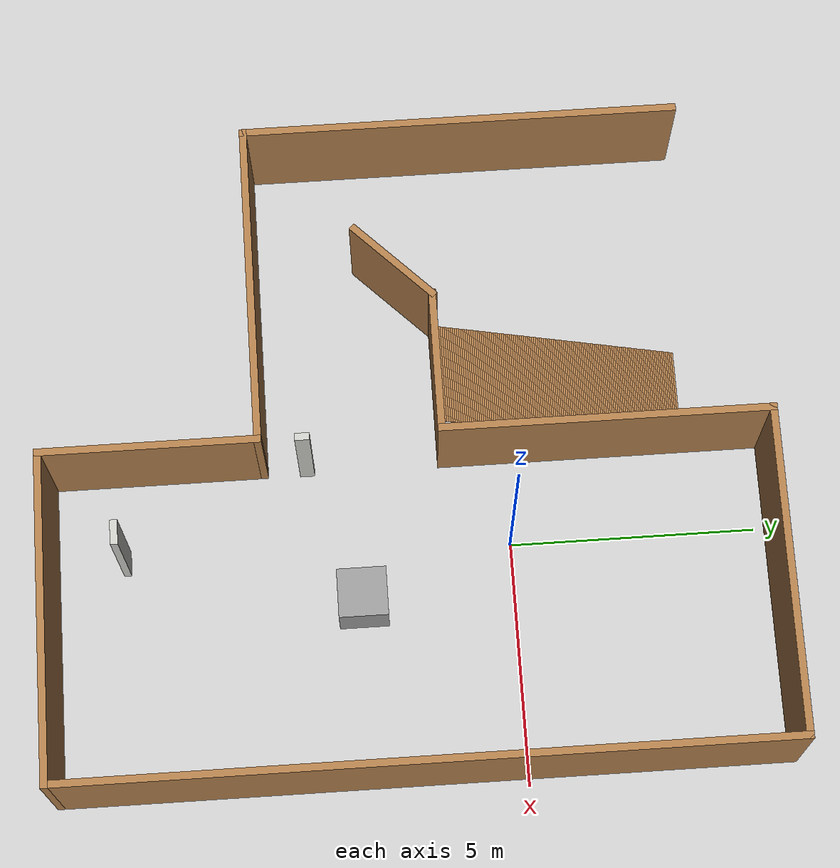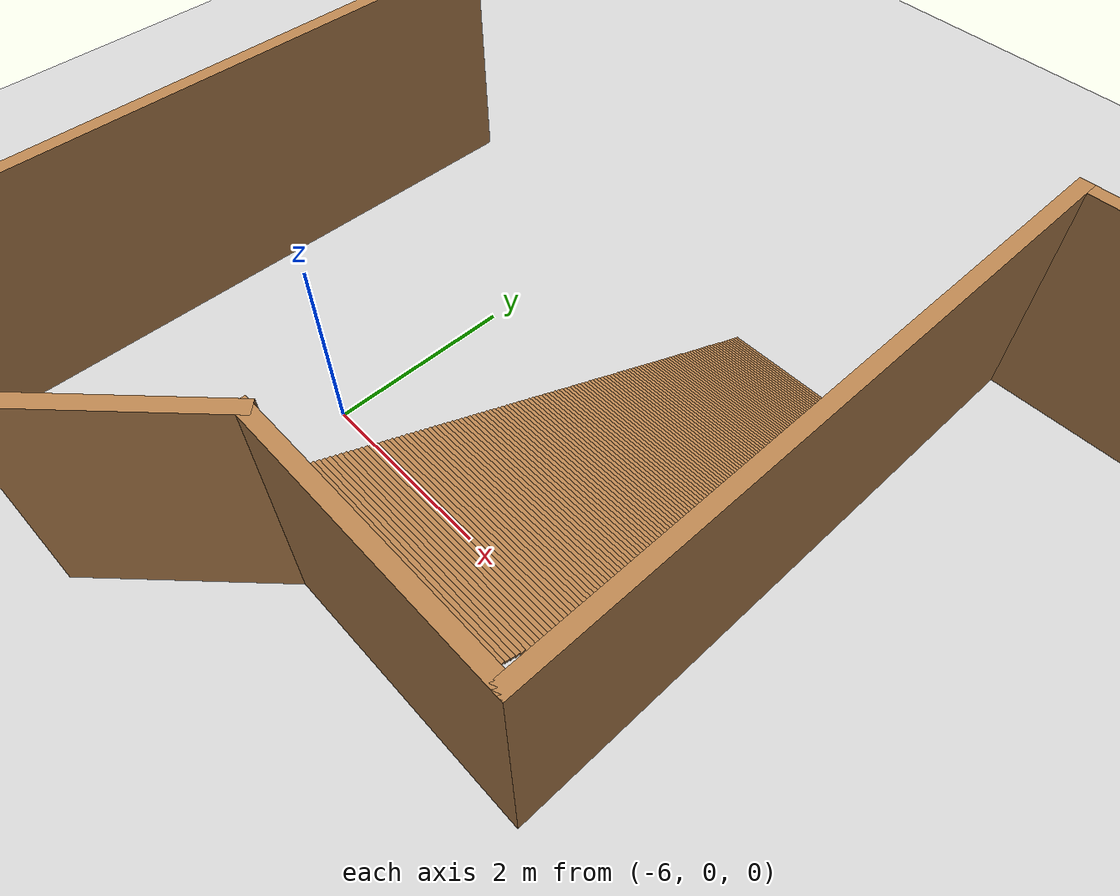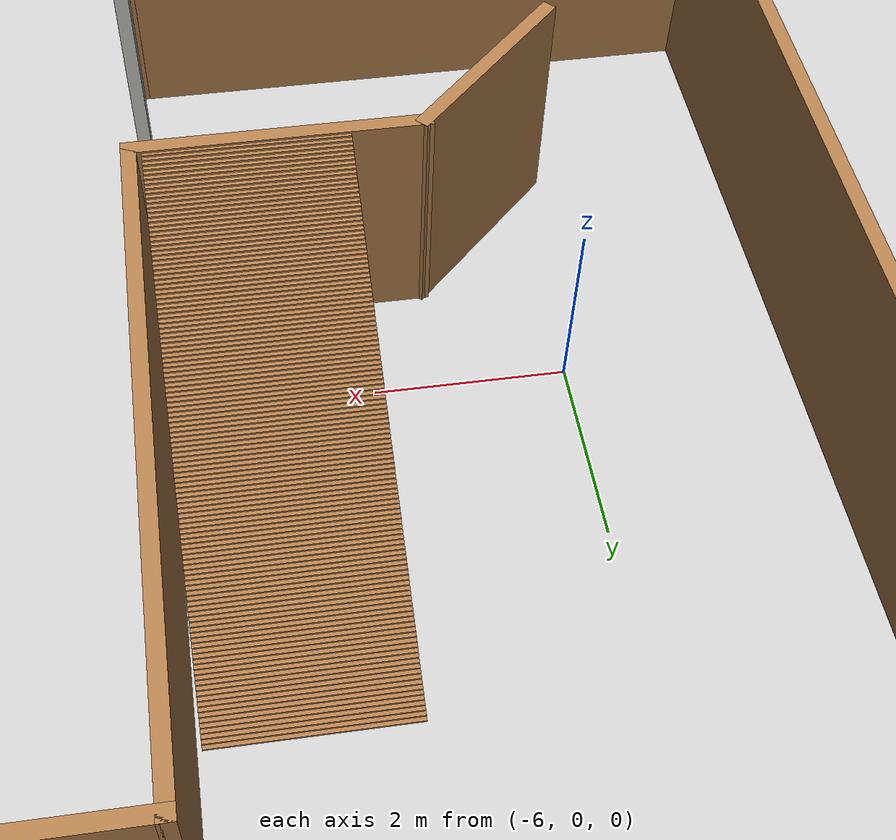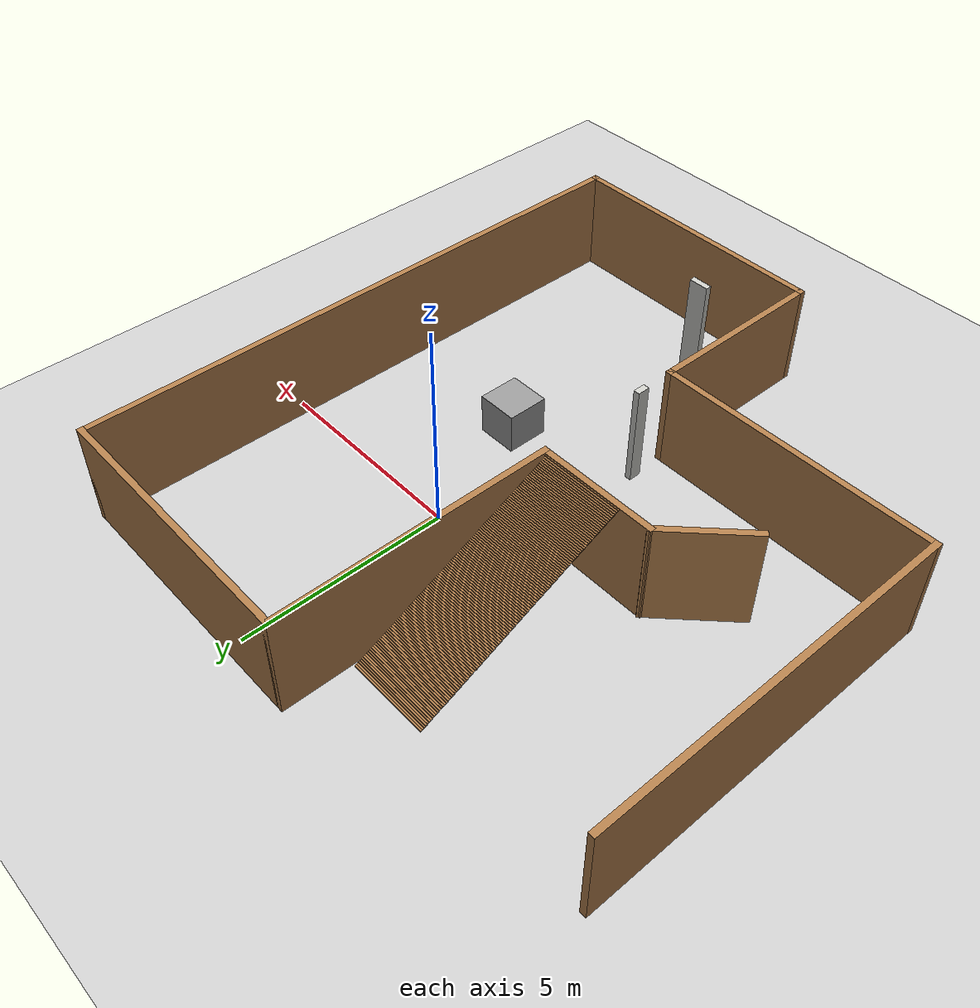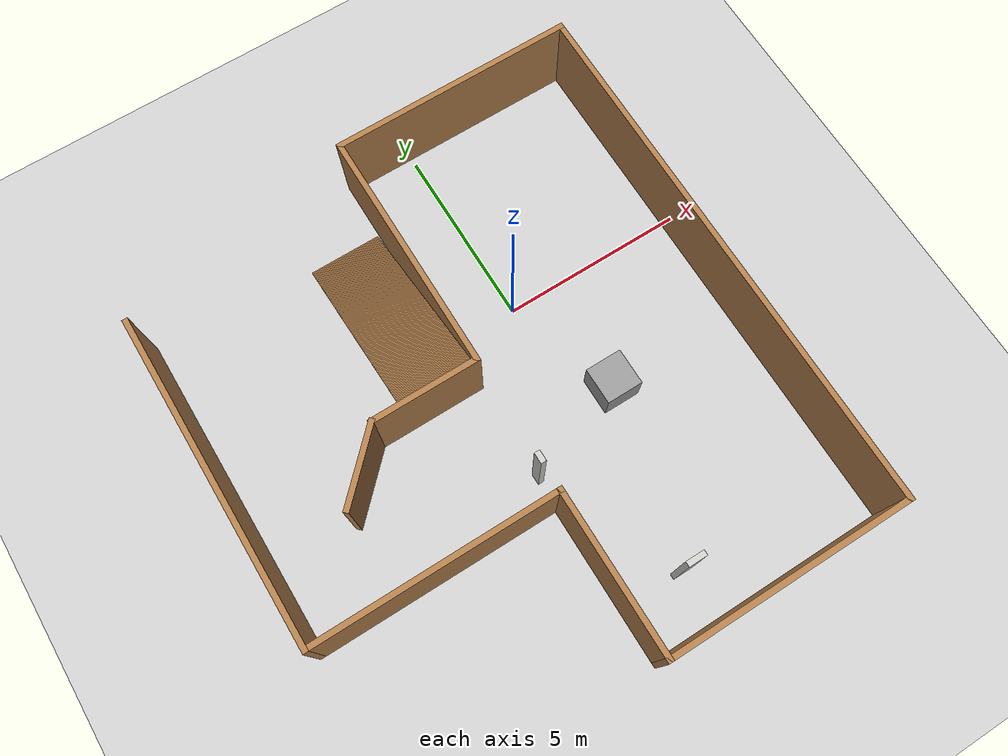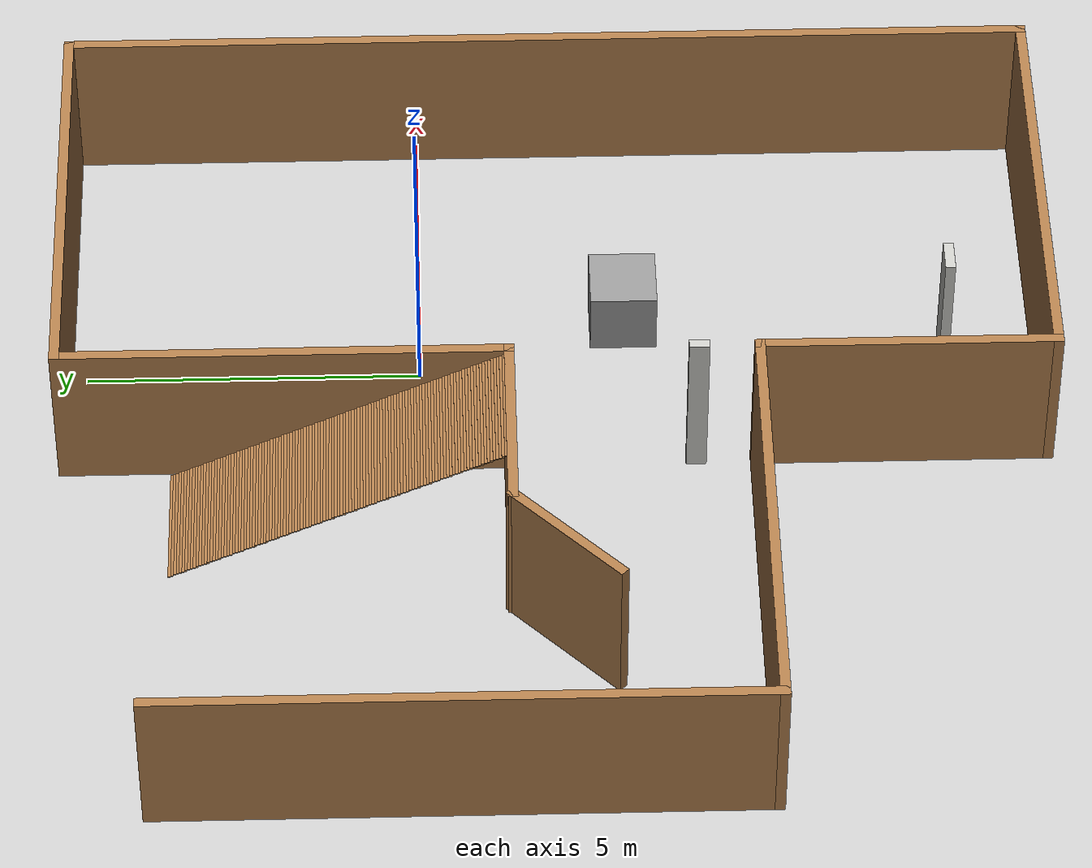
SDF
<sdf version="1.7">
 <world name="default">
  <light name="sun" type="directional">
   <pose>0 0 10 0 -0 0</pose>
   <diffuse>0.8 0.8 0.8 1</diffuse>
   <specular>0.2 0.2 0.2 1</specular>
   <attenuation>
    <range>1000</range>
    <constant>0.9</constant>
    <linear>0.01</linear>
    <quadratic>0.001</quadratic>
   </attenuation>
   <direction>-0.5 0.1 -0.9</direction>
   <spot><inner_angle>0</inner_angle><outer_angle>0</outer_angle><falloff>0</falloff></spot>
  </light>
  <model name="ground_plane">
   <static>1</static>
   <link name="link">
    <collision name="collision">
     <geometry><plane><normal>0 0 1</normal><size>100 100</size></plane></geometry>
     <surface>
      <contact><collide_bitmask>65535</collide_bitmask></contact>
      <friction><ode><mu>100</mu><mu2>50</mu2></ode></friction>
     </surface>
    </collision>
    <visual name="visual">
     <cast_shadows>0</cast_shadows>
     <geometry><plane><normal>0 0 1</normal><size>100 100</size></plane></geometry>
     <material>
      <script><uri>file://media/materials/scripts/gazebo.material</uri><name>Gazebo/Grey</name></script>
     </material>
    </visual>
   </link>
  </model>
  <gravity>0 0 -9.8</gravity>
  <magnetic_field>6e-06 2.3e-05 -4.2e-05</magnetic_field>
  <atmosphere type="adiabatic"/>
  <physics type="ode">
   <max_step_size>0.001</max_step_size>
   <real_time_factor>1</real_time_factor>
   <real_time_update_rate>1000</real_time_update_rate>
  </physics>
  <scene><ambient>0.4 0.4 0.4 1</ambient><background>0.7 0.7 0.7 1</background><shadows>1</shadows></scene>
  <spherical_coordinates>
   <surface_model>EARTH_WGS84</surface_model>
   <latitude_deg>0</latitude_deg>
   <longitude_deg>0</longitude_deg>
   <elevation>0</elevation>
   <heading_deg>0</heading_deg>
  </spherical_coordinates>
  <model name="mundo_normal1">
   <pose>-1.83298 -2.00796 0 0 -0 0</pose>
   <link name="Stairs_4">
    <visual name="Stairs_4_Visual_0">
     <pose>-1.12037 5.70373 0.010417 0 -0 0</pose>
     <geometry><box><size>2 0.041667 0.020833</size></box></geometry>
     <material>
      <script><uri>file://media/materials/scripts/gazebo.material</uri><name>Gazebo/Wood</name></script>
      <ambient>1 1 1 1</ambient>
     </material>
     <meta><layer>0</layer></meta>
    </visual>
    <collision name="Stairs_4_Collision_0">
     <geometry><box><size>2 0.041667 0.020833</size></box></geometry>
     <pose>-1.12037 5.70373 0.010417 0 -0 0</pose>
    </collision>
    <visual name="Stairs_4_Visual_1">
     <pose>-1.12037 5.66206 0.03125 0 -0 0</pose>
     <geometry><box><size>2 0.041667 0.020833</size></box></geometry>
     <material>
      <script><uri>file://media/materials/scripts/gazebo.material</uri><name>Gazebo/Wood</name></script>
      <ambient>1 1 1 1</ambient>
     </material>
     <meta><layer>0</layer></meta>
    </visual>
    <collision name="Stairs_4_Collision_1">
     <geometry><box><size>2 0.041667 0.020833</size></box></geometry>
     <pose>-1.12037 5.66206 0.03125 0 -0 0</pose>
    </collision>
    <visual name="Stairs_4_Visual_2">
     <pose>-1.12037 5.62039 0.052083 0 -0 0</pose>
     <geometry><box><size>2 0.041667 0.020833</size></box></geometry>
     <material>
      <script><uri>file://media/materials/scripts/gazebo.material</uri><name>Gazebo/Wood</name></script>
      <ambient>1 1 1 1</ambient>
     </material>
     <meta><layer>0</layer></meta>
    </visual>
    <collision name="Stairs_4_Collision_2">
     <geometry><box><size>2 0.041667 0.020833</size></box></geometry>
     <pose>-1.12037 5.62039 0.052083 0 -0 0</pose>
    </collision>
    <visual name="Stairs_4_Visual_3">
     <pose>-1.12037 5.57873 0.072917 0 -0 0</pose>
     <geometry><box><size>2 0.041667 0.020833</size></box></geometry>
     <material>
      <script><uri>file://media/materials/scripts/gazebo.material</uri><name>Gazebo/Wood</name></script>
      <ambient>1 1 1 1</ambient>
     </material>
     <meta><layer>0</layer></meta>
    </visual>
    <collision name="Stairs_4_Collision_3">
     <geometry><box><size>2 0.041667 0.020833</size></box></geometry>
     <pose>-1.12037 5.57873 0.072917 0 -0 0</pose>
    </collision>
    <visual name="Stairs_4_Visual_4">
     <pose>-1.12037 5.53706 0.09375 0 -0 0</pose>
     <geometry><box><size>2 0.041667 0.020833</size></box></geometry>
     <material>
      <script><uri>file://media/materials/scripts/gazebo.material</uri><name>Gazebo/Wood</name></script>
      <ambient>1 1 1 1</ambient>
     </material>
     <meta><layer>0</layer></meta>
    </visual>
    <collision name="Stairs_4_Collision_4">
     <geometry><box><size>2 0.041667 0.020833</size></box></geometry>
     <pose>-1.12037 5.53706 0.09375 0 -0 0</pose>
    </collision>
    <visual name="Stairs_4_Visual_5">
     <pose>-1.12037 5.49539 0.114583 0 -0 0</pose>
     <geometry><box><size>2 0.041667 0.020833</size></box></geometry>
     <material>
      <script><uri>file://media/materials/scripts/gazebo.material</uri><name>Gazebo/Wood</name></script>
      <ambient>1 1 1 1</ambient>
     </material>
     <meta><layer>0</layer></meta>
    </visual>
    <collision name="Stairs_4_Collision_5">
     <geometry><box><size>2 0.041667 0.020833</size></box></geometry>
     <pose>-1.12037 5.49539 0.114583 0 -0 0</pose>
    </collision>
    <visual name="Stairs_4_Visual_6">
     <pose>-1.12037 5.45372 0.135417 0 -0 0</pose>
     <geometry><box><size>2 0.041667 0.020833</size></box></geometry>
     <material>
      <script><uri>file://media/materials/scripts/gazebo.material</uri><name>Gazebo/Wood</name></script>
      <ambient>1 1 1 1</ambient>
     </material>
     <meta><layer>0</layer></meta>
    </visual>
    <collision name="Stairs_4_Collision_6">
     <geometry><box><size>2 0.041667 0.020833</size></box></geometry>
     <pose>-1.12037 5.45372 0.135417 0 -0 0</pose>
    </collision>
    <visual name="Stairs_4_Visual_7">
     <pose>-1.12037 5.41206 0.15625 0 -0 0</pose>
     <geometry><box><size>2 0.041667 0.020833</size></box></geometry>
     <material>
      <script><uri>file://media/materials/scripts/gazebo.material</uri><name>Gazebo/Wood</name></script>
      <ambient>1 1 1 1</ambient>
     </material>
     <meta><layer>0</layer></meta>
    </visual>
    <collision name="Stairs_4_Collision_7">
     <geometry><box><size>2 0.041667 0.020833</size></box></geometry>
     <pose>-1.12037 5.41206 0.15625 0 -0 0</pose>
    </collision>
    <visual name="Stairs_4_Visual_8">
     <pose>-1.12037 5.37039 0.177083 0 -0 0</pose>
     <geometry><box><size>2 0.041667 0.020833</size></box></geometry>
     <material>
      <script><uri>file://media/materials/scripts/gazebo.material</uri><name>Gazebo/Wood</name></script>
      <ambient>1 1 1 1</ambient>
     </material>
     <meta><layer>0</layer></meta>
    </visual>
    <collision name="Stairs_4_Collision_8">
     <geometry><box><size>2 0.041667 0.020833</size></box></geometry>
     <pose>-1.12037 5.37039 0.177083 0 -0 0</pose>
    </collision>
    <visual name="Stairs_4_Visual_9">
     <pose>-1.12037 5.32872 0.197917 0 -0 0</pose>
     <geometry><box><size>2 0.041667 0.020833</size></box></geometry>
     <material>
      <script><uri>file://media/materials/scripts/gazebo.material</uri><name>Gazebo/Wood</name></script>
      <ambient>1 1 1 1</ambient>
     </material>
     <meta><layer>0</layer></meta>
    </visual>
    <collision name="Stairs_4_Collision_9">
     <geometry><box><size>2 0.041667 0.020833</size></box></geometry>
     <pose>-1.12037 5.32872 0.197917 0 -0 0</pose>
    </collision>
    <visual name="Stairs_4_Visual_10">
     <pose>-1.12037 5.28706 0.21875 0 -0 0</pose>
     <geometry><box><size>2 0.041667 0.020833</size></box></geometry>
     <material>
      <script><uri>file://media/materials/scripts/gazebo.material</uri><name>Gazebo/Wood</name></script>
      <ambient>1 1 1 1</ambient>
     </material>
     <meta><layer>0</layer></meta>
    </visual>
    <collision name="Stairs_4_Collision_10">
     <geometry><box><size>2 0.041667 0.020833</size></box></geometry>
     <pose>-1.12037 5.28706 0.21875 0 -0 0</pose>
    </collision>
    <visual name="Stairs_4_Visual_11">
     <pose>-1.12037 5.24539 0.239583 0 -0 0</pose>
     <geometry><box><size>2 0.041667 0.020833</size></box></geometry>
     <material>
      <script><uri>file://media/materials/scripts/gazebo.material</uri><name>Gazebo/Wood</name></script>
      <ambient>1 1 1 1</ambient>
     </material>
     <meta><layer>0</layer></meta>
    </visual>
    <collision name="Stairs_4_Collision_11">
     <geometry><box><size>2 0.041667 0.020833</size></box></geometry>
     <pose>-1.12037 5.24539 0.239583 0 -0 0</pose>
    </collision>
    <visual name="Stairs_4_Visual_12">
     <pose>-1.12037 5.20373 0.260417 0 -0 0</pose>
     <geometry><box><size>2 0.041667 0.020833</size></box></geometry>
     <material>
      <script><uri>file://media/materials/scripts/gazebo.material</uri><name>Gazebo/Wood</name></script>
      <ambient>1 1 1 1</ambient>
     </material>
     <meta><layer>0</layer></meta>
    </visual>
    <collision name="Stairs_4_Collision_12">
     <geometry><box><size>2 0.041667 0.020833</size></box></geometry>
     <pose>-1.12037 5.20373 0.260417 0 -0 0</pose>
    </collision>
    <visual name="Stairs_4_Visual_13">
     <pose>-1.12037 5.16206 0.28125 0 -0 0</pose>
     <geometry><box><size>2 0.041667 0.020833</size></box></geometry>
     <material>
      <script><uri>file://media/materials/scripts/gazebo.material</uri><name>Gazebo/Wood</name></script>
      <ambient>1 1 1 1</ambient>
     </material>
     <meta><layer>0</layer></meta>
    </visual>
    <collision name="Stairs_4_Collision_13">
     <geometry><box><size>2 0.041667 0.020833</size></box></geometry>
     <pose>-1.12037 5.16206 0.28125 0 -0 0</pose>
    </collision>
    <visual name="Stairs_4_Visual_14">
     <pose>-1.12037 5.12039 0.302083 0 -0 0</pose>
     <geometry><box><size>2 0.041667 0.020833</size></box></geometry>
     <material>
      <script><uri>file://media/materials/scripts/gazebo.material</uri><name>Gazebo/Wood</name></script>
      <ambient>1 1 1 1</ambient>
     </material>
     <meta><layer>0</layer></meta>
    </visual>
    <collision name="Stairs_4_Collision_14">
     <geometry><box><size>2 0.041667 0.020833</size></box></geometry>
     <pose>-1.12037 5.12039 0.302083 0 -0 0</pose>
    </collision>
    <visual name="Stairs_4_Visual_15">
     <pose>-1.12037 5.07873 0.322917 0 -0 0</pose>
     <geometry><box><size>2 0.041667 0.020833</size></box></geometry>
     <material>
      <script><uri>file://media/materials/scripts/gazebo.material</uri><name>Gazebo/Wood</name></script>
      <ambient>1 1 1 1</ambient>
     </material>
     <meta><layer>0</layer></meta>
    </visual>
    <collision name="Stairs_4_Collision_15">
     <geometry><box><size>2 0.041667 0.020833</size></box></geometry>
     <pose>-1.12037 5.07873 0.322917 0 -0 0</pose>
    </collision>
    <visual name="Stairs_4_Visual_16">
     <pose>-1.12037 5.03706 0.34375 0 -0 0</pose>
     <geometry><box><size>2 0.041667 0.020833</size></box></geometry>
     <material>
      <script><uri>file://media/materials/scripts/gazebo.material</uri><name>Gazebo/Wood</name></script>
      <ambient>1 1 1 1</ambient>
     </material>
     <meta><layer>0</layer></meta>
    </visual>
    <collision name="Stairs_4_Collision_16">
     <geometry><box><size>2 0.041667 0.020833</size></box></geometry>
     <pose>-1.12037 5.03706 0.34375 0 -0 0</pose>
    </collision>
    <visual name="Stairs_4_Visual_17">
     <pose>-1.12037 4.99539 0.364583 0 -0 0</pose>
     <geometry><box><size>2 0.041667 0.020833</size></box></geometry>
     <material>
      <script><uri>file://media/materials/scripts/gazebo.material</uri><name>Gazebo/Wood</name></script>
      <ambient>1 1 1 1</ambient>
     </material>
     <meta><layer>0</layer></meta>
    </visual>
    <collision name="Stairs_4_Collision_17">
     <geometry><box><size>2 0.041667 0.020833</size></box></geometry>
     <pose>-1.12037 4.99539 0.364583 0 -0 0</pose>
    </collision>
    <visual name="Stairs_4_Visual_18">
     <pose>-1.12037 4.95372 0.385417 0 -0 0</pose>
     <geometry><box><size>2 0.041667 0.020833</size></box></geometry>
     <material>
      <script><uri>file://media/materials/scripts/gazebo.material</uri><name>Gazebo/Wood</name></script>
      <ambient>1 1 1 1</ambient>
     </material>
     <meta><layer>0</layer></meta>
    </visual>
    <collision name="Stairs_4_Collision_18">
     <geometry><box><size>2 0.041667 0.020833</size></box></geometry>
     <pose>-1.12037 4.95372 0.385417 0 -0 0</pose>
    </collision>
    <visual name="Stairs_4_Visual_19">
     <pose>-1.12037 4.91206 0.40625 0 -0 0</pose>
     <geometry><box><size>2 0.041667 0.020833</size></box></geometry>
     <material>
      <script><uri>file://media/materials/scripts/gazebo.material</uri><name>Gazebo/Wood</name></script>
      <ambient>1 1 1 1</ambient>
     </material>
     <meta><layer>0</layer></meta>
    </visual>
    <collision name="Stairs_4_Collision_19">
     <geometry><box><size>2 0.041667 0.020833</size></box></geometry>
     <pose>-1.12037 4.91206 0.40625 0 -0 0</pose>
    </collision>
    <visual name="Stairs_4_Visual_20">
     <pose>-1.12037 4.87039 0.427083 0 -0 0</pose>
     <geometry><box><size>2 0.041667 0.020833</size></box></geometry>
     <material>
      <script><uri>file://media/materials/scripts/gazebo.material</uri><name>Gazebo/Wood</name></script>
      <ambient>1 1 1 1</ambient>
     </material>
     <meta><layer>0</layer></meta>
    </visual>
    <collision name="Stairs_4_Collision_20">
     <geometry><box><size>2 0.041667 0.020833</size></box></geometry>
     <pose>-1.12037 4.87039 0.427083 0 -0 0</pose>
    </collision>
    <visual name="Stairs_4_Visual_21">
     <pose>-1.12037 4.82872 0.447917 0 -0 0</pose>
     <geometry><box><size>2 0.041667 0.020833</size></box></geometry>
     <material>
      <script><uri>file://media/materials/scripts/gazebo.material</uri><name>Gazebo/Wood</name></script>
      <ambient>1 1 1 1</ambient>
     </material>
     <meta><layer>0</layer></meta>
    </visual>
    <collision name="Stairs_4_Collision_21">
     <geometry><box><size>2 0.041667 0.020833</size></box></geometry>
     <pose>-1.12037 4.82872 0.447917 0 -0 0</pose>
    </collision>
    <visual name="Stairs_4_Visual_22">
     <pose>-1.12037 4.78706 0.46875 0 -0 0</pose>
     <geometry><box><size>2 0.041667 0.020833</size></box></geometry>
     <material>
      <script><uri>file://media/materials/scripts/gazebo.material</uri><name>Gazebo/Wood</name></script>
      <ambient>1 1 1 1</ambient>
     </material>
     <meta><layer>0</layer></meta>
    </visual>
    <collision name="Stairs_4_Collision_22">
     <geometry><box><size>2 0.041667 0.020833</size></box></geometry>
     <pose>-1.12037 4.78706 0.46875 0 -0 0</pose>
    </collision>
    <visual name="Stairs_4_Visual_23">
     <pose>-1.12037 4.74539 0.489583 0 -0 0</pose>
     <geometry><box><size>2 0.041667 0.020833</size></box></geometry>
     <material>
      <script><uri>file://media/materials/scripts/gazebo.material</uri><name>Gazebo/Wood</name></script>
      <ambient>1 1 1 1</ambient>
     </material>
     <meta><layer>0</layer></meta>
    </visual>
    <collision name="Stairs_4_Collision_23">
     <geometry><box><size>2 0.041667 0.020833</size></box></geometry>
     <pose>-1.12037 4.74539 0.489583 0 -0 0</pose>
    </collision>
    <visual name="Stairs_4_Visual_24">
     <pose>-1.12037 4.70372 0.510417 0 -0 0</pose>
     <geometry><box><size>2 0.041667 0.020833</size></box></geometry>
     <material>
      <script><uri>file://media/materials/scripts/gazebo.material</uri><name>Gazebo/Wood</name></script>
      <ambient>1 1 1 1</ambient>
     </material>
     <meta><layer>0</layer></meta>
    </visual>
    <collision name="Stairs_4_Collision_24">
     <geometry><box><size>2 0.041667 0.020833</size></box></geometry>
     <pose>-1.12037 4.70372 0.510417 0 -0 0</pose>
    </collision>
    <visual name="Stairs_4_Visual_25">
     <pose>-1.12037 4.66206 0.53125 0 -0 0</pose>
     <geometry><box><size>2 0.041667 0.020833</size></box></geometry>
     <material>
      <script><uri>file://media/materials/scripts/gazebo.material</uri><name>Gazebo/Wood</name></script>
      <ambient>1 1 1 1</ambient>
     </material>
     <meta><layer>0</layer></meta>
    </visual>
    <collision name="Stairs_4_Collision_25">
     <geometry><box><size>2 0.041667 0.020833</size></box></geometry>
     <pose>-1.12037 4.66206 0.53125 0 -0 0</pose>
    </collision>
    <visual name="Stairs_4_Visual_26">
     <pose>-1.12037 4.62039 0.552083 0 -0 0</pose>
     <geometry><box><size>2 0.041667 0.020833</size></box></geometry>
     <material>
      <script><uri>file://media/materials/scripts/gazebo.material</uri><name>Gazebo/Wood</name></script>
      <ambient>1 1 1 1</ambient>
     </material>
     <meta><layer>0</layer></meta>
    </visual>
    <collision name="Stairs_4_Collision_26">
     <geometry><box><size>2 0.041667 0.020833</size></box></geometry>
     <pose>-1.12037 4.62039 0.552083 0 -0 0</pose>
    </collision>
    <visual name="Stairs_4_Visual_27">
     <pose>-1.12037 4.57873 0.572917 0 -0 0</pose>
     <geometry><box><size>2 0.041667 0.020833</size></box></geometry>
     <material>
      <script><uri>file://media/materials/scripts/gazebo.material</uri><name>Gazebo/Wood</name></script>
      <ambient>1 1 1 1</ambient>
     </material>
     <meta><layer>0</layer></meta>
    </visual>
    <collision name="Stairs_4_Collision_27">
     <geometry><box><size>2 0.041667 0.020833</size></box></geometry>
     <pose>-1.12037 4.57873 0.572917 0 -0 0</pose>
    </collision>
    <visual name="Stairs_4_Visual_28">
     <pose>-1.12037 4.53706 0.59375 0 -0 0</pose>
     <geometry><box><size>2 0.041667 0.020833</size></box></geometry>
     <material>
      <script><uri>file://media/materials/scripts/gazebo.material</uri><name>Gazebo/Wood</name></script>
      <ambient>1 1 1 1</ambient>
     </material>
     <meta><layer>0</layer></meta>
    </visual>
    <collision name="Stairs_4_Collision_28">
     <geometry><box><size>2 0.041667 0.020833</size></box></geometry>
     <pose>-1.12037 4.53706 0.59375 0 -0 0</pose>
    </collision>
    <visual name="Stairs_4_Visual_29">
     <pose>-1.12037 4.49539 0.614583 0 -0 0</pose>
     <geometry><box><size>2 0.041667 0.020833</size></box></geometry>
     <material>
      <script><uri>file://media/materials/scripts/gazebo.material</uri><name>Gazebo/Wood</name></script>
      <ambient>1 1 1 1</ambient>
     </material>
     <meta><layer>0</layer></meta>
    </visual>
    <collision name="Stairs_4_Collision_29">
     <geometry><box><size>2 0.041667 0.020833</size></box></geometry>
     <pose>-1.12037 4.49539 0.614583 0 -0 0</pose>
    </collision>
    <visual name="Stairs_4_Visual_30">
     <pose>-1.12037 4.45373 0.635417 0 -0 0</pose>
     <geometry><box><size>2 0.041667 0.020833</size></box></geometry>
     <material>
      <script><uri>file://media/materials/scripts/gazebo.material</uri><name>Gazebo/Wood</name></script>
      <ambient>1 1 1 1</ambient>
     </material>
     <meta><layer>0</layer></meta>
    </visual>
    <collision name="Stairs_4_Collision_30">
     <geometry><box><size>2 0.041667 0.020833</size></box></geometry>
     <pose>-1.12037 4.45373 0.635417 0 -0 0</pose>
    </collision>
    <visual name="Stairs_4_Visual_31">
     <pose>-1.12037 4.41206 0.65625 0 -0 0</pose>
     <geometry><box><size>2 0.041667 0.020833</size></box></geometry>
     <material>
      <script><uri>file://media/materials/scripts/gazebo.material</uri><name>Gazebo/Wood</name></script>
      <ambient>1 1 1 1</ambient>
     </material>
     <meta><layer>0</layer></meta>
    </visual>
    <collision name="Stairs_4_Collision_31">
     <geometry><box><size>2 0.041667 0.020833</size></box></geometry>
     <pose>-1.12037 4.41206 0.65625 0 -0 0</pose>
    </collision>
    <visual name="Stairs_4_Visual_32">
     <pose>-1.12037 4.37039 0.677083 0 -0 0</pose>
     <geometry><box><size>2 0.041667 0.020833</size></box></geometry>
     <material>
      <script><uri>file://media/materials/scripts/gazebo.material</uri><name>Gazebo/Wood</name></script>
      <ambient>1 1 1 1</ambient>
     </material>
     <meta><layer>0</layer></meta>
    </visual>
    <collision name="Stairs_4_Collision_32">
     <geometry><box><size>2 0.041667 0.020833</size></box></geometry>
     <pose>-1.12037 4.37039 0.677083 0 -0 0</pose>
    </collision>
    <visual name="Stairs_4_Visual_33">
     <pose>-1.12037 4.32872 0.697917 0 -0 0</pose>
     <geometry><box><size>2 0.041667 0.020833</size></box></geometry>
     <material>
      <script><uri>file://media/materials/scripts/gazebo.material</uri><name>Gazebo/Wood</name></script>
      <ambient>1 1 1 1</ambient>
     </material>
     <meta><layer>0</layer></meta>
    </visual>
    <collision name="Stairs_4_Collision_33">
     <geometry><box><size>2 0.041667 0.020833</size></box></geometry>
     <pose>-1.12037 4.32872 0.697917 0 -0 0</pose>
    </collision>
    <visual name="Stairs_4_Visual_34">
     <pose>-1.12037 4.28706 0.71875 0 -0 0</pose>
     <geometry><box><size>2 0.041667 0.020833</size></box></geometry>
     <material>
      <script><uri>file://media/materials/scripts/gazebo.material</uri><name>Gazebo/Wood</name></script>
      <ambient>1 1 1 1</ambient>
     </material>
     <meta><layer>0</layer></meta>
    </visual>
    <collision name="Stairs_4_Collision_34">
     <geometry><box><size>2 0.041667 0.020833</size></box></geometry>
     <pose>-1.12037 4.28706 0.71875 0 -0 0</pose>
    </collision>
    <visual name="Stairs_4_Visual_35">
     <pose>-1.12037 4.24539 0.739583 0 -0 0</pose>
     <geometry><box><size>2 0.041667 0.020833</size></box></geometry>
     <material>
      <script><uri>file://media/materials/scripts/gazebo.material</uri><name>Gazebo/Wood</name></script>
      <ambient>1 1 1 1</ambient>
     </material>
     <meta><layer>0</layer></meta>
    </visual>
    <collision name="Stairs_4_Collision_35">
     <geometry><box><size>2 0.041667 0.020833</size></box></geometry>
     <pose>-1.12037 4.24539 0.739583 0 -0 0</pose>
    </collision>
    <visual name="Stairs_4_Visual_36">
     <pose>-1.12037 4.20373 0.760417 0 -0 0</pose>
     <geometry><box><size>2 0.041667 0.020833</size></box></geometry>
     <material>
      <script><uri>file://media/materials/scripts/gazebo.material</uri><name>Gazebo/Wood</name></script>
      <ambient>1 1 1 1</ambient>
     </material>
     <meta><layer>0</layer></meta>
    </visual>
    <collision name="Stairs_4_Collision_36">
     <geometry><box><size>2 0.041667 0.020833</size></box></geometry>
     <pose>-1.12037 4.20373 0.760417 0 -0 0</pose>
    </collision>
    <visual name="Stairs_4_Visual_37">
     <pose>-1.12037 4.16206 0.78125 0 -0 0</pose>
     <geometry><box><size>2 0.041667 0.020833</size></box></geometry>
     <material>
      <script><uri>file://media/materials/scripts/gazebo.material</uri><name>Gazebo/Wood</name></script>
      <ambient>1 1 1 1</ambient>
     </material>
     <meta><layer>0</layer></meta>
    </visual>
    <collision name="Stairs_4_Collision_37">
     <geometry><box><size>2 0.041667 0.020833</size></box></geometry>
     <pose>-1.12037 4.16206 0.78125 0 -0 0</pose>
    </collision>
    <visual name="Stairs_4_Visual_38">
     <pose>-1.12037 4.12039 0.802083 0 -0 0</pose>
     <geometry><box><size>2 0.041667 0.020833</size></box></geometry>
     <material>
      <script><uri>file://media/materials/scripts/gazebo.material</uri><name>Gazebo/Wood</name></script>
      <ambient>1 1 1 1</ambient>
     </material>
     <meta><layer>0</layer></meta>
    </visual>
    <collision name="Stairs_4_Collision_38">
     <geometry><box><size>2 0.041667 0.020833</size></box></geometry>
     <pose>-1.12037 4.12039 0.802083 0 -0 0</pose>
    </collision>
    <visual name="Stairs_4_Visual_39">
     <pose>-1.12037 4.07873 0.822917 0 -0 0</pose>
     <geometry><box><size>2 0.041667 0.020833</size></box></geometry>
     <material>
      <script><uri>file://media/materials/scripts/gazebo.material</uri><name>Gazebo/Wood</name></script>
      <ambient>1 1 1 1</ambient>
     </material>
     <meta><layer>0</layer></meta>
    </visual>
    <collision name="Stairs_4_Collision_39">
     <geometry><box><size>2 0.041667 0.020833</size></box></geometry>
     <pose>-1.12037 4.07873 0.822917 0 -0 0</pose>
    </collision>
    <visual name="Stairs_4_Visual_40">
     <pose>-1.12037 4.03706 0.84375 0 -0 0</pose>
     <geometry><box><size>2 0.041667 0.020833</size></box></geometry>
     <material>
      <script><uri>file://media/materials/scripts/gazebo.material</uri><name>Gazebo/Wood</name></script>
      <ambient>1 1 1 1</ambient>
     </material>
     <meta><layer>0</layer></meta>
    </visual>
    <collision name="Stairs_4_Collision_40">
     <geometry><box><size>2 0.041667 0.020833</size></box></geometry>
     <pose>-1.12037 4.03706 0.84375 0 -0 0</pose>
    </collision>
    <visual name="Stairs_4_Visual_41">
     <pose>-1.12037 3.99539 0.864583 0 -0 0</pose>
     <geometry><box><size>2 0.041667 0.020833</size></box></geometry>
     <material>
      <script><uri>file://media/materials/scripts/gazebo.material</uri><name>Gazebo/Wood</name></script>
      <ambient>1 1 1 1</ambient>
     </material>
     <meta><layer>0</layer></meta>
    </visual>
    <collision name="Stairs_4_Collision_41">
     <geometry><box><size>2 0.041667 0.020833</size></box></geometry>
     <pose>-1.12037 3.99539 0.864583 0 -0 0</pose>
    </collision>
    <visual name="Stairs_4_Visual_42">
     <pose>-1.12037 3.95372 0.885417 0 -0 0</pose>
     <geometry><box><size>2 0.041667 0.020833</size></box></geometry>
     <material>
      <script><uri>file://media/materials/scripts/gazebo.material</uri><name>Gazebo/Wood</name></script>
      <ambient>1 1 1 1</ambient>
     </material>
     <meta><layer>0</layer></meta>
    </visual>
    <collision name="Stairs_4_Collision_42">
     <geometry><box><size>2 0.041667 0.020833</size></box></geometry>
     <pose>-1.12037 3.95372 0.885417 0 -0 0</pose>
    </collision>
    <visual name="Stairs_4_Visual_43">
     <pose>-1.12037 3.91206 0.90625 0 -0 0</pose>
     <geometry><box><size>2 0.041667 0.020833</size></box></geometry>
     <material>
      <script><uri>file://media/materials/scripts/gazebo.material</uri><name>Gazebo/Wood</name></script>
      <ambient>1 1 1 1</ambient>
     </material>
     <meta><layer>0</layer></meta>
    </visual>
    <collision name="Stairs_4_Collision_43">
     <geometry><box><size>2 0.041667 0.020833</size></box></geometry>
     <pose>-1.12037 3.91206 0.90625 0 -0 0</pose>
    </collision>
    <visual name="Stairs_4_Visual_44">
     <pose>-1.12037 3.87039 0.927083 0 -0 0</pose>
     <geometry><box><size>2 0.041667 0.020833</size></box></geometry>
     <material>
      <script><uri>file://media/materials/scripts/gazebo.material</uri><name>Gazebo/Wood</name></script>
      <ambient>1 1 1 1</ambient>
     </material>
     <meta><layer>0</layer></meta>
    </visual>
    <collision name="Stairs_4_Collision_44">
     <geometry><box><size>2 0.041667 0.020833</size></box></geometry>
     <pose>-1.12037 3.87039 0.927083 0 -0 0</pose>
    </collision>
    <visual name="Stairs_4_Visual_45">
     <pose>-1.12037 3.82872 0.947917 0 -0 0</pose>
     <geometry><box><size>2 0.041667 0.020833</size></box></geometry>
     <material>
      <script><uri>file://media/materials/scripts/gazebo.material</uri><name>Gazebo/Wood</name></script>
      <ambient>1 1 1 1</ambient>
     </material>
     <meta><layer>0</layer></meta>
    </visual>
    <collision name="Stairs_4_Collision_45">
     <geometry><box><size>2 0.041667 0.020833</size></box></geometry>
     <pose>-1.12037 3.82872 0.947917 0 -0 0</pose>
    </collision>
    <visual name="Stairs_4_Visual_46">
     <pose>-1.12037 3.78706 0.96875 0 -0 0</pose>
     <geometry><box><size>2 0.041667 0.020833</size></box></geometry>
     <material>
      <script><uri>file://media/materials/scripts/gazebo.material</uri><name>Gazebo/Wood</name></script>
      <ambient>1 1 1 1</ambient>
     </material>
     <meta><layer>0</layer></meta>
    </visual>
    <collision name="Stairs_4_Collision_46">
     <geometry><box><size>2 0.041667 0.020833</size></box></geometry>
     <pose>-1.12037 3.78706 0.96875 0 -0 0</pose>
    </collision>
    <visual name="Stairs_4_Visual_47">
     <pose>-1.12037 3.74539 0.989583 0 -0 0</pose>
     <geometry><box><size>2 0.041667 0.020833</size></box></geometry>
     <material>
      <script><uri>file://media/materials/scripts/gazebo.material</uri><name>Gazebo/Wood</name></script>
      <ambient>1 1 1 1</ambient>
     </material>
     <meta><layer>0</layer></meta>
    </visual>
    <collision name="Stairs_4_Collision_47">
     <geometry><box><size>2 0.041667 0.020833</size></box></geometry>
     <pose>-1.12037 3.74539 0.989583 0 -0 0</pose>
    </collision>
    <visual name="Stairs_4_Visual_48">
     <pose>-1.12037 3.70372 1.01042 0 -0 0</pose>
     <geometry><box><size>2 0.041667 0.020833</size></box></geometry>
     <material>
      <script><uri>file://media/materials/scripts/gazebo.material</uri><name>Gazebo/Wood</name></script>
      <ambient>1 1 1 1</ambient>
     </material>
     <meta><layer>0</layer></meta>
    </visual>
    <collision name="Stairs_4_Collision_48">
     <geometry><box><size>2 0.041667 0.020833</size></box></geometry>
     <pose>-1.12037 3.70372 1.01042 0 -0 0</pose>
    </collision>
    <visual name="Stairs_4_Visual_49">
     <pose>-1.12037 3.66206 1.03125 0 -0 0</pose>
     <geometry><box><size>2 0.041667 0.020833</size></box></geometry>
     <material>
      <script><uri>file://media/materials/scripts/gazebo.material</uri><name>Gazebo/Wood</name></script>
      <ambient>1 1 1 1</ambient>
     </material>
     <meta><layer>0</layer></meta>
    </visual>
    <collision name="Stairs_4_Collision_49">
     <geometry><box><size>2 0.041667 0.020833</size></box></geometry>
     <pose>-1.12037 3.66206 1.03125 0 -0 0</pose>
    </collision>
    <visual name="Stairs_4_Visual_50">
     <pose>-1.12037 3.62039 1.05208 0 -0 0</pose>
     <geometry><box><size>2 0.041667 0.020833</size></box></geometry>
     <material>
      <script><uri>file://media/materials/scripts/gazebo.material</uri><name>Gazebo/Wood</name></script>
      <ambient>1 1 1 1</ambient>
     </material>
     <meta><layer>0</layer></meta>
    </visual>
    <collision name="Stairs_4_Collision_50">
     <geometry><box><size>2 0.041667 0.020833</size></box></geometry>
     <pose>-1.12037 3.62039 1.05208 0 -0 0</pose>
    </collision>
    <visual name="Stairs_4_Visual_51">
     <pose>-1.12037 3.57872 1.07292 0 -0 0</pose>
     <geometry><box><size>2 0.041667 0.020833</size></box></geometry>
     <material>
      <script><uri>file://media/materials/scripts/gazebo.material</uri><name>Gazebo/Wood</name></script>
      <ambient>1 1 1 1</ambient>
     </material>
     <meta><layer>0</layer></meta>
    </visual>
    <collision name="Stairs_4_Collision_51">
     <geometry><box><size>2 0.041667 0.020833</size></box></geometry>
     <pose>-1.12037 3.57872 1.07292 0 -0 0</pose>
    </collision>
    <visual name="Stairs_4_Visual_52">
     <pose>-1.12037 3.53706 1.09375 0 -0 0</pose>
     <geometry><box><size>2 0.041667 0.020833</size></box></geometry>
     <material>
      <script><uri>file://media/materials/scripts/gazebo.material</uri><name>Gazebo/Wood</name></script>
      <ambient>1 1 1 1</ambient>
     </material>
     <meta><layer>0</layer></meta>
    </visual>
    <collision name="Stairs_4_Collision_52">
     <geometry><box><size>2 0.041667 0.020833</size></box></geometry>
     <pose>-1.12037 3.53706 1.09375 0 -0 0</pose>
    </collision>
    <visual name="Stairs_4_Visual_53">
     <pose>-1.12037 3.49539 1.11458 0 -0 0</pose>
     <geometry><box><size>2 0.041667 0.020833</size></box></geometry>
     <material>
      <script><uri>file://media/materials/scripts/gazebo.material</uri><name>Gazebo/Wood</name></script>
      <ambient>1 1 1 1</ambient>
     </material>
     <meta><layer>0</layer></meta>
    </visual>
    <collision name="Stairs_4_Collision_53">
     <geometry><box><size>2 0.041667 0.020833</size></box></geometry>
     <pose>-1.12037 3.49539 1.11458 0 -0 0</pose>
    </collision>
    <visual name="Stairs_4_Visual_54">
     <pose>-1.12037 3.45372 1.13542 0 -0 0</pose>
     <geometry><box><size>2 0.041667 0.020833</size></box></geometry>
     <material>
      <script><uri>file://media/materials/scripts/gazebo.material</uri><name>Gazebo/Wood</name></script>
      <ambient>1 1 1 1</ambient>
     </material>
     <meta><layer>0</layer></meta>
    </visual>
    <collision name="Stairs_4_Collision_54">
     <geometry><box><size>2 0.041667 0.020833</size></box></geometry>
     <pose>-1.12037 3.45372 1.13542 0 -0 0</pose>
    </collision>
    <visual name="Stairs_4_Visual_55">
     <pose>-1.12037 3.41206 1.15625 0 -0 0</pose>
     <geometry><box><size>2 0.041667 0.020833</size></box></geometry>
     <material>
      <script><uri>file://media/materials/scripts/gazebo.material</uri><name>Gazebo/Wood</name></script>
      <ambient>1 1 1 1</ambient>
     </material>
     <meta><layer>0</layer></meta>
    </visual>
    <collision name="Stairs_4_Collision_55">
     <geometry><box><size>2 0.041667 0.020833</size></box></geometry>
     <pose>-1.12037 3.41206 1.15625 0 -0 0</pose>
    </collision>
    <visual name="Stairs_4_Visual_56">
     <pose>-1.12037 3.37039 1.17708 0 -0 0</pose>
     <geometry><box><size>2 0.041667 0.020833</size></box></geometry>
     <material>
      <script><uri>file://media/materials/scripts/gazebo.material</uri><name>Gazebo/Wood</name></script>
      <ambient>1 1 1 1</ambient>
     </material>
     <meta><layer>0</layer></meta>
    </visual>
    <collision name="Stairs_4_Collision_56">
     <geometry><box><size>2 0.041667 0.020833</size></box></geometry>
     <pose>-1.12037 3.37039 1.17708 0 -0 0</pose>
    </collision>
    <visual name="Stairs_4_Visual_57">
     <pose>-1.12037 3.32872 1.19792 0 -0 0</pose>
     <geometry><box><size>2 0.041667 0.020833</size></box></geometry>
     <material>
      <script><uri>file://media/materials/scripts/gazebo.material</uri><name>Gazebo/Wood</name></script>
      <ambient>1 1 1 1</ambient>
     </material>
     <meta><layer>0</layer></meta>
    </visual>
    <collision name="Stairs_4_Collision_57">
     <geometry><box><size>2 0.041667 0.020833</size></box></geometry>
     <pose>-1.12037 3.32872 1.19792 0 -0 0</pose>
    </collision>
    <visual name="Stairs_4_Visual_58">
     <pose>-1.12037 3.28706 1.21875 0 -0 0</pose>
     <geometry><box><size>2 0.041667 0.020833</size></box></geometry>
     <material>
      <script><uri>file://media/materials/scripts/gazebo.material</uri><name>Gazebo/Wood</name></script>
      <ambient>1 1 1 1</ambient>
     </material>
     <meta><layer>0</layer></meta>
    </visual>
    <collision name="Stairs_4_Collision_58">
     <geometry><box><size>2 0.041667 0.020833</size></box></geometry>
     <pose>-1.12037 3.28706 1.21875 0 -0 0</pose>
    </collision>
    <visual name="Stairs_4_Visual_59">
     <pose>-1.12037 3.24539 1.23958 0 -0 0</pose>
     <geometry><box><size>2 0.041667 0.020833</size></box></geometry>
     <material>
      <script><uri>file://media/materials/scripts/gazebo.material</uri><name>Gazebo/Wood</name></script>
      <ambient>1 1 1 1</ambient>
     </material>
     <meta><layer>0</layer></meta>
    </visual>
    <collision name="Stairs_4_Collision_59">
     <geometry><box><size>2 0.041667 0.020833</size></box></geometry>
     <pose>-1.12037 3.24539 1.23958 0 -0 0</pose>
    </collision>
    <visual name="Stairs_4_Visual_60">
     <pose>-1.12037 3.20372 1.26042 0 -0 0</pose>
     <geometry><box><size>2 0.041667 0.020833</size></box></geometry>
     <material>
      <script><uri>file://media/materials/scripts/gazebo.material</uri><name>Gazebo/Wood</name></script>
      <ambient>1 1 1 1</ambient>
     </material>
     <meta><layer>0</layer></meta>
    </visual>
    <collision name="Stairs_4_Collision_60">
     <geometry><box><size>2 0.041667 0.020833</size></box></geometry>
     <pose>-1.12037 3.20372 1.26042 0 -0 0</pose>
    </collision>
    <visual name="Stairs_4_Visual_61">
     <pose>-1.12037 3.16206 1.28125 0 -0 0</pose>
     <geometry><box><size>2 0.041667 0.020833</size></box></geometry>
     <material>
      <script><uri>file://media/materials/scripts/gazebo.material</uri><name>Gazebo/Wood</name></script>
      <ambient>1 1 1 1</ambient>
     </material>
     <meta><layer>0</layer></meta>
    </visual>
    <collision name="Stairs_4_Collision_61">
     <geometry><box><size>2 0.041667 0.020833</size></box></geometry>
     <pose>-1.12037 3.16206 1.28125 0 -0 0</pose>
    </collision>
    <visual name="Stairs_4_Visual_62">
     <pose>-1.12037 3.12039 1.30208 0 -0 0</pose>
     <geometry><box><size>2 0.041667 0.020833</size></box></geometry>
     <material>
      <script><uri>file://media/materials/scripts/gazebo.material</uri><name>Gazebo/Wood</name></script>
      <ambient>1 1 1 1</ambient>
     </material>
     <meta><layer>0</layer></meta>
    </visual>
    <collision name="Stairs_4_Collision_62">
     <geometry><box><size>2 0.041667 0.020833</size></box></geometry>
     <pose>-1.12037 3.12039 1.30208 0 -0 0</pose>
    </collision>
    <visual name="Stairs_4_Visual_63">
     <pose>-1.12037 3.07872 1.32292 0 -0 0</pose>
     <geometry><box><size>2 0.041667 0.020833</size></box></geometry>
     <material>
      <script><uri>file://media/materials/scripts/gazebo.material</uri><name>Gazebo/Wood</name></script>
      <ambient>1 1 1 1</ambient>
     </material>
     <meta><layer>0</layer></meta>
    </visual>
    <collision name="Stairs_4_Collision_63">
     <geometry><box><size>2 0.041667 0.020833</size></box></geometry>
     <pose>-1.12037 3.07872 1.32292 0 -0 0</pose>
    </collision>
    <visual name="Stairs_4_Visual_64">
     <pose>-1.12037 3.03706 1.34375 0 -0 0</pose>
     <geometry><box><size>2 0.041667 0.020833</size></box></geometry>
     <material>
      <script><uri>file://media/materials/scripts/gazebo.material</uri><name>Gazebo/Wood</name></script>
      <ambient>1 1 1 1</ambient>
     </material>
     <meta><layer>0</layer></meta>
    </visual>
    <collision name="Stairs_4_Collision_64">
     <geometry><box><size>2 0.041667 0.020833</size></box></geometry>
     <pose>-1.12037 3.03706 1.34375 0 -0 0</pose>
    </collision>
    <visual name="Stairs_4_Visual_65">
     <pose>-1.12037 2.99539 1.36458 0 -0 0</pose>
     <geometry><box><size>2 0.041667 0.020833</size></box></geometry>
     <material>
      <script><uri>file://media/materials/scripts/gazebo.material</uri><name>Gazebo/Wood</name></script>
      <ambient>1 1 1 1</ambient>
     </material>
     <meta><layer>0</layer></meta>
    </visual>
    <collision name="Stairs_4_Collision_65">
     <geometry><box><size>2 0.041667 0.020833</size></box></geometry>
     <pose>-1.12037 2.99539 1.36458 0 -0 0</pose>
    </collision>
    <visual name="Stairs_4_Visual_66">
     <pose>-1.12037 2.95372 1.38542 0 -0 0</pose>
     <geometry><box><size>2 0.041667 0.020833</size></box></geometry>
     <material>
      <script><uri>file://media/materials/scripts/gazebo.material</uri><name>Gazebo/Wood</name></script>
      <ambient>1 1 1 1</ambient>
     </material>
     <meta><layer>0</layer></meta>
    </visual>
    <collision name="Stairs_4_Collision_66">
     <geometry><box><size>2 0.041667 0.020833</size></box></geometry>
     <pose>-1.12037 2.95372 1.38542 0 -0 0</pose>
    </collision>
    <visual name="Stairs_4_Visual_67">
     <pose>-1.12037 2.91206 1.40625 0 -0 0</pose>
     <geometry><box><size>2 0.041667 0.020833</size></box></geometry>
     <material>
      <script><uri>file://media/materials/scripts/gazebo.material</uri><name>Gazebo/Wood</name></script>
      <ambient>1 1 1 1</ambient>
     </material>
     <meta><layer>0</layer></meta>
    </visual>
    <collision name="Stairs_4_Collision_67">
     <geometry><box><size>2 0.041667 0.020833</size></box></geometry>
     <pose>-1.12037 2.91206 1.40625 0 -0 0</pose>
    </collision>
    <visual name="Stairs_4_Visual_68">
     <pose>-1.12037 2.87039 1.42708 0 -0 0</pose>
     <geometry><box><size>2 0.041667 0.020833</size></box></geometry>
     <material>
      <script><uri>file://media/materials/scripts/gazebo.material</uri><name>Gazebo/Wood</name></script>
      <ambient>1 1 1 1</ambient>
     </material>
     <meta><layer>0</layer></meta>
    </visual>
    <collision name="Stairs_4_Collision_68">
     <geometry><box><size>2 0.041667 0.020833</size></box></geometry>
     <pose>-1.12037 2.87039 1.42708 0 -0 0</pose>
    </collision>
    <visual name="Stairs_4_Visual_69">
     <pose>-1.12037 2.82872 1.44792 0 -0 0</pose>
     <geometry><box><size>2 0.041667 0.020833</size></box></geometry>
     <material>
      <script><uri>file://media/materials/scripts/gazebo.material</uri><name>Gazebo/Wood</name></script>
      <ambient>1 1 1 1</ambient>
     </material>
     <meta><layer>0</layer></meta>
    </visual>
    <collision name="Stairs_4_Collision_69">
     <geometry><box><size>2 0.041667 0.020833</size></box></geometry>
     <pose>-1.12037 2.82872 1.44792 0 -0 0</pose>
    </collision>
    <visual name="Stairs_4_Visual_70">
     <pose>-1.12037 2.78706 1.46875 0 -0 0</pose>
     <geometry><box><size>2 0.041667 0.020833</size></box></geometry>
     <material>
      <script><uri>file://media/materials/scripts/gazebo.material</uri><name>Gazebo/Wood</name></script>
      <ambient>1 1 1 1</ambient>
     </material>
     <meta><layer>0</layer></meta>
    </visual>
    <collision name="Stairs_4_Collision_70">
     <geometry><box><size>2 0.041667 0.020833</size></box></geometry>
     <pose>-1.12037 2.78706 1.46875 0 -0 0</pose>
    </collision>
    <visual name="Stairs_4_Visual_71">
     <pose>-1.12037 2.74539 1.48958 0 -0 0</pose>
     <geometry><box><size>2 0.041667 0.020833</size></box></geometry>
     <material>
      <script><uri>file://media/materials/scripts/gazebo.material</uri><name>Gazebo/Wood</name></script>
      <ambient>1 1 1 1</ambient>
     </material>
     <meta><layer>0</layer></meta>
    </visual>
    <collision name="Stairs_4_Collision_71">
     <geometry><box><size>2 0.041667 0.020833</size></box></geometry>
     <pose>-1.12037 2.74539 1.48958 0 -0 0</pose>
    </collision>
    <visual name="Stairs_4_Visual_72">
     <pose>-1.12037 2.70372 1.51042 0 -0 0</pose>
     <geometry><box><size>2 0.041667 0.020833</size></box></geometry>
     <material>
      <script><uri>file://media/materials/scripts/gazebo.material</uri><name>Gazebo/Wood</name></script>
      <ambient>1 1 1 1</ambient>
     </material>
     <meta><layer>0</layer></meta>
    </visual>
    <collision name="Stairs_4_Collision_72">
     <geometry><box><size>2 0.041667 0.020833</size></box></geometry>
     <pose>-1.12037 2.70372 1.51042 0 -0 0</pose>
    </collision>
    <visual name="Stairs_4_Visual_73">
     <pose>-1.12037 2.66206 1.53125 0 -0 0</pose>
     <geometry><box><size>2 0.041667 0.020833</size></box></geometry>
     <material>
      <script><uri>file://media/materials/scripts/gazebo.material</uri><name>Gazebo/Wood</name></script>
      <ambient>1 1 1 1</ambient>
     </material>
     <meta><layer>0</layer></meta>
    </visual>
    <collision name="Stairs_4_Collision_73">
     <geometry><box><size>2 0.041667 0.020833</size></box></geometry>
     <pose>-1.12037 2.66206 1.53125 0 -0 0</pose>
    </collision>
    <visual name="Stairs_4_Visual_74">
     <pose>-1.12037 2.62039 1.55208 0 -0 0</pose>
     <geometry><box><size>2 0.041667 0.020833</size></box></geometry>
     <material>
      <script><uri>file://media/materials/scripts/gazebo.material</uri><name>Gazebo/Wood</name></script>
      <ambient>1 1 1 1</ambient>
     </material>
     <meta><layer>0</layer></meta>
    </visual>
    <collision name="Stairs_4_Collision_74">
     <geometry><box><size>2 0.041667 0.020833</size></box></geometry>
     <pose>-1.12037 2.62039 1.55208 0 -0 0</pose>
    </collision>
    <visual name="Stairs_4_Visual_75">
     <pose>-1.12037 2.57872 1.57292 0 -0 0</pose>
     <geometry><box><size>2 0.041667 0.020833</size></box></geometry>
     <material>
      <script><uri>file://media/materials/scripts/gazebo.material</uri><name>Gazebo/Wood</name></script>
      <ambient>1 1 1 1</ambient>
     </material>
     <meta><layer>0</layer></meta>
    </visual>
    <collision name="Stairs_4_Collision_75">
     <geometry><box><size>2 0.041667 0.020833</size></box></geometry>
     <pose>-1.12037 2.57872 1.57292 0 -0 0</pose>
    </collision>
    <visual name="Stairs_4_Visual_76">
     <pose>-1.12037 2.53706 1.59375 0 -0 0</pose>
     <geometry><box><size>2 0.041667 0.020833</size></box></geometry>
     <material>
      <script><uri>file://media/materials/scripts/gazebo.material</uri><name>Gazebo/Wood</name></script>
      <ambient>1 1 1 1</ambient>
     </material>
     <meta><layer>0</layer></meta>
    </visual>
    <collision name="Stairs_4_Collision_76">
     <geometry><box><size>2 0.041667 0.020833</size></box></geometry>
     <pose>-1.12037 2.53706 1.59375 0 -0 0</pose>
    </collision>
    <visual name="Stairs_4_Visual_77">
     <pose>-1.12037 2.49539 1.61458 0 -0 0</pose>
     <geometry><box><size>2 0.041667 0.020833</size></box></geometry>
     <material>
      <script><uri>file://media/materials/scripts/gazebo.material</uri><name>Gazebo/Wood</name></script>
      <ambient>1 1 1 1</ambient>
     </material>
     <meta><layer>0</layer></meta>
    </visual>
    <collision name="Stairs_4_Collision_77">
     <geometry><box><size>2 0.041667 0.020833</size></box></geometry>
     <pose>-1.12037 2.49539 1.61458 0 -0 0</pose>
    </collision>
    <visual name="Stairs_4_Visual_78">
     <pose>-1.12037 2.45372 1.63542 0 -0 0</pose>
     <geometry><box><size>2 0.041667 0.020833</size></box></geometry>
     <material>
      <script><uri>file://media/materials/scripts/gazebo.material</uri><name>Gazebo/Wood</name></script>
      <ambient>1 1 1 1</ambient>
     </material>
     <meta><layer>0</layer></meta>
    </visual>
    <collision name="Stairs_4_Collision_78">
     <geometry><box><size>2 0.041667 0.020833</size></box></geometry>
     <pose>-1.12037 2.45372 1.63542 0 -0 0</pose>
    </collision>
    <visual name="Stairs_4_Visual_79">
     <pose>-1.12037 2.41206 1.65625 0 -0 0</pose>
     <geometry><box><size>2 0.041667 0.020833</size></box></geometry>
     <material>
      <script><uri>file://media/materials/scripts/gazebo.material</uri><name>Gazebo/Wood</name></script>
      <ambient>1 1 1 1</ambient>
     </material>
     <meta><layer>0</layer></meta>
    </visual>
    <collision name="Stairs_4_Collision_79">
     <geometry><box><size>2 0.041667 0.020833</size></box></geometry>
     <pose>-1.12037 2.41206 1.65625 0 -0 0</pose>
    </collision>
    <visual name="Stairs_4_Visual_80">
     <pose>-1.12037 2.37039 1.67708 0 -0 0</pose>
     <geometry><box><size>2 0.041667 0.020833</size></box></geometry>
     <material>
      <script><uri>file://media/materials/scripts/gazebo.material</uri><name>Gazebo/Wood</name></script>
      <ambient>1 1 1 1</ambient>
     </material>
     <meta><layer>0</layer></meta>
    </visual>
    <collision name="Stairs_4_Collision_80">
     <geometry><box><size>2 0.041667 0.020833</size></box></geometry>
     <pose>-1.12037 2.37039 1.67708 0 -0 0</pose>
    </collision>
    <visual name="Stairs_4_Visual_81">
     <pose>-1.12037 2.32872 1.69792 0 -0 0</pose>
     <geometry><box><size>2 0.041667 0.020833</size></box></geometry>
     <material>
      <script><uri>file://media/materials/scripts/gazebo.material</uri><name>Gazebo/Wood</name></script>
      <ambient>1 1 1 1</ambient>
     </material>
     <meta><layer>0</layer></meta>
    </visual>
    <collision name="Stairs_4_Collision_81">
     <geometry><box><size>2 0.041667 0.020833</size></box></geometry>
     <pose>-1.12037 2.32872 1.69792 0 -0 0</pose>
    </collision>
    <visual name="Stairs_4_Visual_82">
     <pose>-1.12037 2.28706 1.71875 0 -0 0</pose>
     <geometry><box><size>2 0.041667 0.020833</size></box></geometry>
     <material>
      <script><uri>file://media/materials/scripts/gazebo.material</uri><name>Gazebo/Wood</name></script>
      <ambient>1 1 1 1</ambient>
     </material>
     <meta><layer>0</layer></meta>
    </visual>
    <collision name="Stairs_4_Collision_82">
     <geometry><box><size>2 0.041667 0.020833</size></box></geometry>
     <pose>-1.12037 2.28706 1.71875 0 -0 0</pose>
    </collision>
    <visual name="Stairs_4_Visual_83">
     <pose>-1.12037 2.24539 1.73958 0 -0 0</pose>
     <geometry><box><size>2 0.041667 0.020833</size></box></geometry>
     <material>
      <script><uri>file://media/materials/scripts/gazebo.material</uri><name>Gazebo/Wood</name></script>
      <ambient>1 1 1 1</ambient>
     </material>
     <meta><layer>0</layer></meta>
    </visual>
    <collision name="Stairs_4_Collision_83">
     <geometry><box><size>2 0.041667 0.020833</size></box></geometry>
     <pose>-1.12037 2.24539 1.73958 0 -0 0</pose>
    </collision>
    <visual name="Stairs_4_Visual_84">
     <pose>-1.12037 2.20372 1.76042 0 -0 0</pose>
     <geometry><box><size>2 0.041667 0.020833</size></box></geometry>
     <material>
      <script><uri>file://media/materials/scripts/gazebo.material</uri><name>Gazebo/Wood</name></script>
      <ambient>1 1 1 1</ambient>
     </material>
     <meta><layer>0</layer></meta>
    </visual>
    <collision name="Stairs_4_Collision_84">
     <geometry><box><size>2 0.041667 0.020833</size></box></geometry>
     <pose>-1.12037 2.20372 1.76042 0 -0 0</pose>
    </collision>
    <visual name="Stairs_4_Visual_85">
     <pose>-1.12037 2.16206 1.78125 0 -0 0</pose>
     <geometry><box><size>2 0.041667 0.020833</size></box></geometry>
     <material>
      <script><uri>file://media/materials/scripts/gazebo.material</uri><name>Gazebo/Wood</name></script>
      <ambient>1 1 1 1</ambient>
     </material>
     <meta><layer>0</layer></meta>
    </visual>
    <collision name="Stairs_4_Collision_85">
     <geometry><box><size>2 0.041667 0.020833</size></box></geometry>
     <pose>-1.12037 2.16206 1.78125 0 -0 0</pose>
    </collision>
    <visual name="Stairs_4_Visual_86">
     <pose>-1.12037 2.12039 1.80208 0 -0 0</pose>
     <geometry><box><size>2 0.041667 0.020833</size></box></geometry>
     <material>
      <script><uri>file://media/materials/scripts/gazebo.material</uri><name>Gazebo/Wood</name></script>
      <ambient>1 1 1 1</ambient>
     </material>
     <meta><layer>0</layer></meta>
    </visual>
    <collision name="Stairs_4_Collision_86">
     <geometry><box><size>2 0.041667 0.020833</size></box></geometry>
     <pose>-1.12037 2.12039 1.80208 0 -0 0</pose>
    </collision>
    <visual name="Stairs_4_Visual_87">
     <pose>-1.12037 2.07872 1.82292 0 -0 0</pose>
     <geometry><box><size>2 0.041667 0.020833</size></box></geometry>
     <material>
      <script><uri>file://media/materials/scripts/gazebo.material</uri><name>Gazebo/Wood</name></script>
      <ambient>1 1 1 1</ambient>
     </material>
     <meta><layer>0</layer></meta>
    </visual>
    <collision name="Stairs_4_Collision_87">
     <geometry><box><size>2 0.041667 0.020833</size></box></geometry>
     <pose>-1.12037 2.07872 1.82292 0 -0 0</pose>
    </collision>
    <visual name="Stairs_4_Visual_88">
     <pose>-1.12037 2.03706 1.84375 0 -0 0</pose>
     <geometry><box><size>2 0.041667 0.020833</size></box></geometry>
     <material>
      <script><uri>file://media/materials/scripts/gazebo.material</uri><name>Gazebo/Wood</name></script>
      <ambient>1 1 1 1</ambient>
     </material>
     <meta><layer>0</layer></meta>
    </visual>
    <collision name="Stairs_4_Collision_88">
     <geometry><box><size>2 0.041667 0.020833</size></box></geometry>
     <pose>-1.12037 2.03706 1.84375 0 -0 0</pose>
    </collision>
    <visual name="Stairs_4_Visual_89">
     <pose>-1.12037 1.99539 1.86458 0 -0 0</pose>
     <geometry><box><size>2 0.041667 0.020833</size></box></geometry>
     <material>
      <script><uri>file://media/materials/scripts/gazebo.material</uri><name>Gazebo/Wood</name></script>
      <ambient>1 1 1 1</ambient>
     </material>
     <meta><layer>0</layer></meta>
    </visual>
    <collision name="Stairs_4_Collision_89">
     <geometry><box><size>2 0.041667 0.020833</size></box></geometry>
     <pose>-1.12037 1.99539 1.86458 0 -0 0</pose>
    </collision>
    <visual name="Stairs_4_Visual_90">
     <pose>-1.12037 1.95372 1.88542 0 -0 0</pose>
     <geometry><box><size>2 0.041667 0.020833</size></box></geometry>
     <material>
      <script><uri>file://media/materials/scripts/gazebo.material</uri><name>Gazebo/Wood</name></script>
      <ambient>1 1 1 1</ambient>
     </material>
     <meta><layer>0</layer></meta>
    </visual>
    <collision name="Stairs_4_Collision_90">
     <geometry><box><size>2 0.041667 0.020833</size></box></geometry>
     <pose>-1.12037 1.95372 1.88542 0 -0 0</pose>
    </collision>
    <visual name="Stairs_4_Visual_91">
     <pose>-1.12037 1.91206 1.90625 0 -0 0</pose>
     <geometry><box><size>2 0.041667 0.020833</size></box></geometry>
     <material>
      <script><uri>file://media/materials/scripts/gazebo.material</uri><name>Gazebo/Wood</name></script>
      <ambient>1 1 1 1</ambient>
     </material>
     <meta><layer>0</layer></meta>
    </visual>
    <collision name="Stairs_4_Collision_91">
     <geometry><box><size>2 0.041667 0.020833</size></box></geometry>
     <pose>-1.12037 1.91206 1.90625 0 -0 0</pose>
    </collision>
    <visual name="Stairs_4_Visual_92">
     <pose>-1.12037 1.87039 1.92708 0 -0 0</pose>
     <geometry><box><size>2 0.041667 0.020833</size></box></geometry>
     <material>
      <script><uri>file://media/materials/scripts/gazebo.material</uri><name>Gazebo/Wood</name></script>
      <ambient>1 1 1 1</ambient>
     </material>
     <meta><layer>0</layer></meta>
    </visual>
    <collision name="Stairs_4_Collision_92">
     <geometry><box><size>2 0.041667 0.020833</size></box></geometry>
     <pose>-1.12037 1.87039 1.92708 0 -0 0</pose>
    </collision>
    <visual name="Stairs_4_Visual_93">
     <pose>-1.12037 1.82872 1.94792 0 -0 0</pose>
     <geometry><box><size>2 0.041667 0.020833</size></box></geometry>
     <material>
      <script><uri>file://media/materials/scripts/gazebo.material</uri><name>Gazebo/Wood</name></script>
      <ambient>1 1 1 1</ambient>
     </material>
     <meta><layer>0</layer></meta>
    </visual>
    <collision name="Stairs_4_Collision_93">
     <geometry><box><size>2 0.041667 0.020833</size></box></geometry>
     <pose>-1.12037 1.82872 1.94792 0 -0 0</pose>
    </collision>
    <visual name="Stairs_4_Visual_94">
     <pose>-1.12037 1.78706 1.96875 0 -0 0</pose>
     <geometry><box><size>2 0.041667 0.020833</size></box></geometry>
     <material>
      <script><uri>file://media/materials/scripts/gazebo.material</uri><name>Gazebo/Wood</name></script>
      <ambient>1 1 1 1</ambient>
     </material>
     <meta><layer>0</layer></meta>
    </visual>
    <collision name="Stairs_4_Collision_94">
     <geometry><box><size>2 0.041667 0.020833</size></box></geometry>
     <pose>-1.12037 1.78706 1.96875 0 -0 0</pose>
    </collision>
    <visual name="Stairs_4_Visual_95">
     <pose>-1.12037 1.74539 1.98958 0 -0 0</pose>
     <geometry><box><size>2 0.041667 0.020833</size></box></geometry>
     <material>
      <script><uri>file://media/materials/scripts/gazebo.material</uri><name>Gazebo/Wood</name></script>
      <ambient>1 1 1 1</ambient>
     </material>
     <meta><layer>0</layer></meta>
    </visual>
    <collision name="Stairs_4_Collision_95">
     <geometry><box><size>2 0.041667 0.020833</size></box></geometry>
     <pose>-1.12037 1.74539 1.98958 0 -0 0</pose>
    </collision>
    <visual name="Stairs_4_Visual_96">
     <pose>-1.12037 1.70372 2.01042 0 -0 0</pose>
     <geometry><box><size>2 0.041667 0.020833</size></box></geometry>
     <material>
      <script><uri>file://media/materials/scripts/gazebo.material</uri><name>Gazebo/Wood</name></script>
      <ambient>1 1 1 1</ambient>
     </material>
     <meta><layer>0</layer></meta>
    </visual>
    <collision name="Stairs_4_Collision_96">
     <geometry><box><size>2 0.041667 0.020833</size></box></geometry>
     <pose>-1.12037 1.70372 2.01042 0 -0 0</pose>
    </collision>
    <visual name="Stairs_4_Visual_97">
     <pose>-1.12037 1.66206 2.03125 0 -0 0</pose>
     <geometry><box><size>2 0.041667 0.020833</size></box></geometry>
     <material>
      <script><uri>file://media/materials/scripts/gazebo.material</uri><name>Gazebo/Wood</name></script>
      <ambient>1 1 1 1</ambient>
     </material>
     <meta><layer>0</layer></meta>
    </visual>
    <collision name="Stairs_4_Collision_97">
     <geometry><box><size>2 0.041667 0.020833</size></box></geometry>
     <pose>-1.12037 1.66206 2.03125 0 -0 0</pose>
    </collision>
    <visual name="Stairs_4_Visual_98">
     <pose>-1.12037 1.62039 2.05208 0 -0 0</pose>
     <geometry><box><size>2 0.041667 0.020833</size></box></geometry>
     <material>
      <script><uri>file://media/materials/scripts/gazebo.material</uri><name>Gazebo/Wood</name></script>
      <ambient>1 1 1 1</ambient>
     </material>
     <meta><layer>0</layer></meta>
    </visual>
    <collision name="Stairs_4_Collision_98">
     <geometry><box><size>2 0.041667 0.020833</size></box></geometry>
     <pose>-1.12037 1.62039 2.05208 0 -0 0</pose>
    </collision>
    <visual name="Stairs_4_Visual_99">
     <pose>-1.12037 1.57872 2.07292 0 -0 0</pose>
     <geometry><box><size>2 0.041667 0.020833</size></box></geometry>
     <material>
      <script><uri>file://media/materials/scripts/gazebo.material</uri><name>Gazebo/Wood</name></script>
      <ambient>1 1 1 1</ambient>
     </material>
     <meta><layer>0</layer></meta>
    </visual>
    <collision name="Stairs_4_Collision_99">
     <geometry><box><size>2 0.041667 0.020833</size></box></geometry>
     <pose>-1.12037 1.57872 2.07292 0 -0 0</pose>
    </collision>
    <visual name="Stairs_4_Visual_100">
     <pose>-1.12037 1.53706 2.09375 0 -0 0</pose>
     <geometry><box><size>2 0.041667 0.020833</size></box></geometry>
     <material>
      <script><uri>file://media/materials/scripts/gazebo.material</uri><name>Gazebo/Wood</name></script>
      <ambient>1 1 1 1</ambient>
     </material>
     <meta><layer>0</layer></meta>
    </visual>
    <collision name="Stairs_4_Collision_100">
     <geometry><box><size>2 0.041667 0.020833</size></box></geometry>
     <pose>-1.12037 1.53706 2.09375 0 -0 0</pose>
    </collision>
    <visual name="Stairs_4_Visual_101">
     <pose>-1.12037 1.49539 2.11458 0 -0 0</pose>
     <geometry><box><size>2 0.041667 0.020833</size></box></geometry>
     <material>
      <script><uri>file://media/materials/scripts/gazebo.material</uri><name>Gazebo/Wood</name></script>
      <ambient>1 1 1 1</ambient>
     </material>
     <meta><layer>0</layer></meta>
    </visual>
    <collision name="Stairs_4_Collision_101">
     <geometry><box><size>2 0.041667 0.020833</size></box></geometry>
     <pose>-1.12037 1.49539 2.11458 0 -0 0</pose>
    </collision>
    <visual name="Stairs_4_Visual_102">
     <pose>-1.12037 1.45372 2.13542 0 -0 0</pose>
     <geometry><box><size>2 0.041667 0.020833</size></box></geometry>
     <material>
      <script><uri>file://media/materials/scripts/gazebo.material</uri><name>Gazebo/Wood</name></script>
      <ambient>1 1 1 1</ambient>
     </material>
     <meta><layer>0</layer></meta>
    </visual>
    <collision name="Stairs_4_Collision_102">
     <geometry><box><size>2 0.041667 0.020833</size></box></geometry>
     <pose>-1.12037 1.45372 2.13542 0 -0 0</pose>
    </collision>
    <visual name="Stairs_4_Visual_103">
     <pose>-1.12037 1.41206 2.15625 0 -0 0</pose>
     <geometry><box><size>2 0.041667 0.020833</size></box></geometry>
     <material>
      <script><uri>file://media/materials/scripts/gazebo.material</uri><name>Gazebo/Wood</name></script>
      <ambient>1 1 1 1</ambient>
     </material>
     <meta><layer>0</layer></meta>
    </visual>
    <collision name="Stairs_4_Collision_103">
     <geometry><box><size>2 0.041667 0.020833</size></box></geometry>
     <pose>-1.12037 1.41206 2.15625 0 -0 0</pose>
    </collision>
    <visual name="Stairs_4_Visual_104">
     <pose>-1.12037 1.37039 2.17708 0 -0 0</pose>
     <geometry><box><size>2 0.041667 0.020833</size></box></geometry>
     <material>
      <script><uri>file://media/materials/scripts/gazebo.material</uri><name>Gazebo/Wood</name></script>
      <ambient>1 1 1 1</ambient>
     </material>
     <meta><layer>0</layer></meta>
    </visual>
    <collision name="Stairs_4_Collision_104">
     <geometry><box><size>2 0.041667 0.020833</size></box></geometry>
     <pose>-1.12037 1.37039 2.17708 0 -0 0</pose>
    </collision>
    <visual name="Stairs_4_Visual_105">
     <pose>-1.12037 1.32872 2.19792 0 -0 0</pose>
     <geometry><box><size>2 0.041667 0.020833</size></box></geometry>
     <material>
      <script><uri>file://media/materials/scripts/gazebo.material</uri><name>Gazebo/Wood</name></script>
      <ambient>1 1 1 1</ambient>
     </material>
     <meta><layer>0</layer></meta>
    </visual>
    <collision name="Stairs_4_Collision_105">
     <geometry><box><size>2 0.041667 0.020833</size></box></geometry>
     <pose>-1.12037 1.32872 2.19792 0 -0 0</pose>
    </collision>
    <visual name="Stairs_4_Visual_106">
     <pose>-1.12037 1.28706 2.21875 0 -0 0</pose>
     <geometry><box><size>2 0.041667 0.020833</size></box></geometry>
     <material>
      <script><uri>file://media/materials/scripts/gazebo.material</uri><name>Gazebo/Wood</name></script>
      <ambient>1 1 1 1</ambient>
     </material>
     <meta><layer>0</layer></meta>
    </visual>
    <collision name="Stairs_4_Collision_106">
     <geometry><box><size>2 0.041667 0.020833</size></box></geometry>
     <pose>-1.12037 1.28706 2.21875 0 -0 0</pose>
    </collision>
    <visual name="Stairs_4_Visual_107">
     <pose>-1.12037 1.24539 2.23958 0 -0 0</pose>
     <geometry><box><size>2 0.041667 0.020833</size></box></geometry>
     <material>
      <script><uri>file://media/materials/scripts/gazebo.material</uri><name>Gazebo/Wood</name></script>
      <ambient>1 1 1 1</ambient>
     </material>
     <meta><layer>0</layer></meta>
    </visual>
    <collision name="Stairs_4_Collision_107">
     <geometry><box><size>2 0.041667 0.020833</size></box></geometry>
     <pose>-1.12037 1.24539 2.23958 0 -0 0</pose>
    </collision>
    <visual name="Stairs_4_Visual_108">
     <pose>-1.12037 1.20372 2.26042 0 -0 0</pose>
     <geometry><box><size>2 0.041667 0.020833</size></box></geometry>
     <material>
      <script><uri>file://media/materials/scripts/gazebo.material</uri><name>Gazebo/Wood</name></script>
      <ambient>1 1 1 1</ambient>
     </material>
     <meta><layer>0</layer></meta>
    </visual>
    <collision name="Stairs_4_Collision_108">
     <geometry><box><size>2 0.041667 0.020833</size></box></geometry>
     <pose>-1.12037 1.20372 2.26042 0 -0 0</pose>
    </collision>
    <visual name="Stairs_4_Visual_109">
     <pose>-1.12037 1.16206 2.28125 0 -0 0</pose>
     <geometry><box><size>2 0.041667 0.020833</size></box></geometry>
     <material>
      <script><uri>file://media/materials/scripts/gazebo.material</uri><name>Gazebo/Wood</name></script>
      <ambient>1 1 1 1</ambient>
     </material>
     <meta><layer>0</layer></meta>
    </visual>
    <collision name="Stairs_4_Collision_109">
     <geometry><box><size>2 0.041667 0.020833</size></box></geometry>
     <pose>-1.12037 1.16206 2.28125 0 -0 0</pose>
    </collision>
    <visual name="Stairs_4_Visual_110">
     <pose>-1.12037 1.12039 2.30208 0 -0 0</pose>
     <geometry><box><size>2 0.041667 0.020833</size></box></geometry>
     <material>
      <script><uri>file://media/materials/scripts/gazebo.material</uri><name>Gazebo/Wood</name></script>
      <ambient>1 1 1 1</ambient>
     </material>
     <meta><layer>0</layer></meta>
    </visual>
    <collision name="Stairs_4_Collision_110">
     <geometry><box><size>2 0.041667 0.020833</size></box></geometry>
     <pose>-1.12037 1.12039 2.30208 0 -0 0</pose>
    </collision>
    <visual name="Stairs_4_Visual_111">
     <pose>-1.12037 1.07872 2.32292 0 -0 0</pose>
     <geometry><box><size>2 0.041667 0.020833</size></box></geometry>
     <material>
      <script><uri>file://media/materials/scripts/gazebo.material</uri><name>Gazebo/Wood</name></script>
      <ambient>1 1 1 1</ambient>
     </material>
     <meta><layer>0</layer></meta>
    </visual>
    <collision name="Stairs_4_Collision_111">
     <geometry><box><size>2 0.041667 0.020833</size></box></geometry>
     <pose>-1.12037 1.07872 2.32292 0 -0 0</pose>
    </collision>
    <visual name="Stairs_4_Visual_112">
     <pose>-1.12037 1.03706 2.34375 0 -0 0</pose>
     <geometry><box><size>2 0.041667 0.020833</size></box></geometry>
     <material>
      <script><uri>file://media/materials/scripts/gazebo.material</uri><name>Gazebo/Wood</name></script>
      <ambient>1 1 1 1</ambient>
     </material>
     <meta><layer>0</layer></meta>
    </visual>
    <collision name="Stairs_4_Collision_112">
     <geometry><box><size>2 0.041667 0.020833</size></box></geometry>
     <pose>-1.12037 1.03706 2.34375 0 -0 0</pose>
    </collision>
    <visual name="Stairs_4_Visual_113">
     <pose>-1.12037 0.995391 2.36458 0 -0 0</pose>
     <geometry><box><size>2 0.041667 0.020833</size></box></geometry>
     <material>
      <script><uri>file://media/materials/scripts/gazebo.material</uri><name>Gazebo/Wood</name></script>
      <ambient>1 1 1 1</ambient>
     </material>
     <meta><layer>0</layer></meta>
    </visual>
    <collision name="Stairs_4_Collision_113">
     <geometry><box><size>2 0.041667 0.020833</size></box></geometry>
     <pose>-1.12037 0.995391 2.36458 0 -0 0</pose>
    </collision>
    <visual name="Stairs_4_Visual_114">
     <pose>-1.12037 0.953724 2.38542 0 -0 0</pose>
     <geometry><box><size>2 0.041667 0.020833</size></box></geometry>
     <material>
      <script><uri>file://media/materials/scripts/gazebo.material</uri><name>Gazebo/Wood</name></script>
      <ambient>1 1 1 1</ambient>
     </material>
     <meta><layer>0</layer></meta>
    </visual>
    <collision name="Stairs_4_Collision_114">
     <geometry><box><size>2 0.041667 0.020833</size></box></geometry>
     <pose>-1.12037 0.953724 2.38542 0 -0 0</pose>
    </collision>
    <visual name="Stairs_4_Visual_115">
     <pose>-1.12037 0.912058 2.40625 0 -0 0</pose>
     <geometry><box><size>2 0.041667 0.020833</size></box></geometry>
     <material>
      <script><uri>file://media/materials/scripts/gazebo.material</uri><name>Gazebo/Wood</name></script>
      <ambient>1 1 1 1</ambient>
     </material>
     <meta><layer>0</layer></meta>
    </visual>
    <collision name="Stairs_4_Collision_115">
     <geometry><box><size>2 0.041667 0.020833</size></box></geometry>
     <pose>-1.12037 0.912058 2.40625 0 -0 0</pose>
    </collision>
    <visual name="Stairs_4_Visual_116">
     <pose>-1.12037 0.870391 2.42708 0 -0 0</pose>
     <geometry><box><size>2 0.041667 0.020833</size></box></geometry>
     <material>
      <script><uri>file://media/materials/scripts/gazebo.material</uri><name>Gazebo/Wood</name></script>
      <ambient>1 1 1 1</ambient>
     </material>
     <meta><layer>0</layer></meta>
    </visual>
    <collision name="Stairs_4_Collision_116">
     <geometry><box><size>2 0.041667 0.020833</size></box></geometry>
     <pose>-1.12037 0.870391 2.42708 0 -0 0</pose>
    </collision>
    <visual name="Stairs_4_Visual_117">
     <pose>-1.12037 0.828725 2.44792 0 -0 0</pose>
     <geometry><box><size>2 0.041667 0.020833</size></box></geometry>
     <material>
      <script><uri>file://media/materials/scripts/gazebo.material</uri><name>Gazebo/Wood</name></script>
      <ambient>1 1 1 1</ambient>
     </material>
     <meta><layer>0</layer></meta>
    </visual>
    <collision name="Stairs_4_Collision_117">
     <geometry><box><size>2 0.041667 0.020833</size></box></geometry>
     <pose>-1.12037 0.828725 2.44792 0 -0 0</pose>
    </collision>
    <visual name="Stairs_4_Visual_118">
     <pose>-1.12037 0.787058 2.46875 0 -0 0</pose>
     <geometry><box><size>2 0.041667 0.020833</size></box></geometry>
     <material>
      <script><uri>file://media/materials/scripts/gazebo.material</uri><name>Gazebo/Wood</name></script>
      <ambient>1 1 1 1</ambient>
     </material>
     <meta><layer>0</layer></meta>
    </visual>
    <collision name="Stairs_4_Collision_118">
     <geometry><box><size>2 0.041667 0.020833</size></box></geometry>
     <pose>-1.12037 0.787058 2.46875 0 -0 0</pose>
    </collision>
    <visual name="Stairs_4_Visual_119">
     <pose>-1.12037 0.745391 2.48958 0 -0 0</pose>
     <geometry><box><size>2 0.041667 0.020833</size></box></geometry>
     <material>
      <script><uri>file://media/materials/scripts/gazebo.material</uri><name>Gazebo/Wood</name></script>
      <ambient>1 1 1 1</ambient>
     </material>
     <meta><layer>0</layer></meta>
    </visual>
    <collision name="Stairs_4_Collision_119">
     <geometry><box><size>2 0.041667 0.020833</size></box></geometry>
     <pose>-1.12037 0.745391 2.48958 0 -0 0</pose>
    </collision>
   </link>
   <link name="Wall_0">
    <collision name="Wall_0_Collision">
     <geometry><box><size>6.75 0.15 2.5</size></box></geometry>
     <pose>0 0 1.25 0 -0 0</pose>
    </collision>
    <visual name="Wall_0_Visual">
     <pose>0 0 1.25 0 -0 0</pose>
     <geometry><box><size>6.75 0.15 2.5</size></box></geometry>
     <material>
      <script><uri>file://media/materials/scripts/gazebo.material</uri><name>Gazebo/Wood</name></script>
      <ambient>1 1 1 1</ambient>
     </material>
     <meta><layer>0</layer></meta>
    </visual>
    <pose>0 4 0 0 -0 1.5708</pose>
   </link>
   <link name="Wall_1">
    <collision name="Wall_1_Collision">
     <geometry><box><size>6.75 0.15 2.5</size></box></geometry>
     <pose>0 0 1.25 0 -0 0</pose>
    </collision>
    <visual name="Wall_1_Visual">
     <pose>0 0 1.25 0 -0 0</pose>
     <geometry><box><size>6.75 0.15 2.5</size></box></geometry>
     <material>
      <script><uri>file://media/materials/scripts/gazebo.material</uri><name>Gazebo/Wood</name></script>
      <ambient>1 1 1 1</ambient>
     </material>
     <meta><layer>0</layer></meta>
    </visual>
    <pose>3.3 7.3 0 0 -0 0</pose>
   </link>
   <link name="Wall_10">
    <collision name="Wall_10_Collision">
     <geometry><box><size>3 0.15 2.5</size></box></geometry>
     <pose>0 0 1.25 0 -0 0</pose>
    </collision>
    <visual name="Wall_10_Visual">
     <pose>0 0 1.25 0 -0 0</pose>
     <geometry><box><size>3 0.15 2.5</size></box></geometry>
     <material>
      <script><uri>file://media/materials/scripts/gazebo.material</uri><name>Gazebo/Wood</name></script>
      <ambient>1 1 1 1</ambient>
     </material>
     <meta><layer>0</layer></meta>
    </visual>
    <pose>-1.425 0.7 0 0 -0 3.14159</pose>
   </link>
   <link name="Wall_11">
    <collision name="Wall_11_Collision">
     <geometry><box><size>2.25 0.15 2.5</size></box></geometry>
     <pose>0 0 1.25 0 -0 0</pose>
    </collision>
    <visual name="Wall_11_Visual">
     <pose>0 0 1.25 0 -0 0</pose>
     <geometry><box><size>2.25 0.15 2.5</size></box></geometry>
     <material>
      <script><uri>file://media/materials/scripts/gazebo.material</uri><name>Gazebo/Wood</name></script>
      <ambient>1 1 1 1</ambient>
     </material>
     <meta><layer>0</layer></meta>
    </visual>
    <pose>-3.59246 -0.042462 0 0 -0 -2.35619</pose>
   </link>
   <link name="Wall_13">
    <collision name="Wall_13_Collision">
     <geometry><box><size>0.5 0.15 2.5</size></box></geometry>
     <pose>0 0 1.25 0 -0 0</pose>
    </collision>
    <visual name="Wall_13_Visual">
     <pose>0 0 1.25 0 -0 0</pose>
     <geometry><box><size>0.5 0.15 2.5</size></box></geometry>
     <material>
      <script><uri>file://media/materials/scripts/gazebo.material</uri><name>Gazebo/CeilingTiled</name></script>
      <ambient>1 1 1 1</ambient>
     </material>
     <meta><layer>0</layer></meta>
    </visual>
    <pose>1.7247 -5.83749 0 0 -0 0</pose>
   </link>
   <link name="Wall_16">
    <collision name="Wall_16_Collision">
     <geometry><box><size>0.3 0.15 2.5</size></box></geometry>
     <pose>0 0 1.25 0 -0 0</pose>
    </collision>
    <visual name="Wall_16_Visual">
     <pose>0 0 1.25 0 -0 0</pose>
     <geometry><box><size>0.3 0.15 2.5</size></box></geometry>
     <material>
      <script><uri>file://media/materials/scripts/gazebo.material</uri><name>Gazebo/CeilingTiled</name></script>
      <ambient>1 1 1 1</ambient>
     </material>
     <meta><layer>0</layer></meta>
    </visual>
    <pose>0.012384 -2.06921 0 0 -0 -1.5708</pose>
   </link>
   <link name="Wall_2">
    <collision name="Wall_2_Collision">
     <geometry><box><size>14.75 0.15 2.5</size></box></geometry>
     <pose>0 0 1.25 0 -0 0</pose>
    </collision>
    <visual name="Wall_2_Visual">
     <pose>0 0 1.25 0 -0 0</pose>
     <geometry><box><size>14.75 0.15 2.5</size></box></geometry>
     <material>
      <script><uri>file://media/materials/scripts/gazebo.material</uri><name>Gazebo/Wood</name></script>
      <ambient>1 1 1 1</ambient>
     </material>
     <meta><layer>0</layer></meta>
    </visual>
    <pose>6.6 0 0 0 -0 -1.5708</pose>
   </link>
   <link name="Wall_3">
    <collision name="Wall_3_Collision">
     <geometry><box><size>6.75 0.15 2.5</size></box></geometry>
     <pose>0 0 1.25 0 -0 0</pose>
    </collision>
    <visual name="Wall_3_Visual">
     <pose>0 0 1.25 0 -0 0</pose>
     <geometry><box><size>6.75 0.15 2.5</size></box></geometry>
     <material>
      <script><uri>file://media/materials/scripts/gazebo.material</uri><name>Gazebo/Wood</name></script>
      <ambient>1 1 1 1</ambient>
     </material>
     <meta><layer>0</layer></meta>
    </visual>
    <pose>3.3 -7.3 0 0 -0 3.14159</pose>
   </link>
   <link name="Wall_6">
    <collision name="Wall_6_Collision">
     <geometry><box><size>4.5 0.15 2.5</size></box></geometry>
     <pose>0 0 1.25 0 -0 0</pose>
    </collision>
    <visual name="Wall_6_Visual">
     <pose>0 0 1.25 0 -0 0</pose>
     <geometry><box><size>4.5 0.15 2.5</size></box></geometry>
     <material>
      <script><uri>file://media/materials/scripts/gazebo.material</uri><name>Gazebo/Wood</name></script>
      <ambient>1 1 1 1</ambient>
     </material>
     <meta><layer>0</layer></meta>
    </visual>
    <pose>0 -5.125 0 0 -0 1.5708</pose>
   </link>
   <link name="Wall_7">
    <collision name="Wall_7_Collision">
     <geometry><box><size>6.75 0.15 2.5</size></box></geometry>
     <pose>0 0 1.25 0 -0 0</pose>
    </collision>
    <visual name="Wall_7_Visual">
     <pose>0 0 1.25 0 -0 0</pose>
     <geometry><box><size>6.75 0.15 2.5</size></box></geometry>
     <material>
      <script><uri>file://media/materials/scripts/gazebo.material</uri><name>Gazebo/Wood</name></script>
      <ambient>1 1 1 1</ambient>
     </material>
     <meta><layer>0</layer></meta>
    </visual>
    <pose>-3.3 -2.95 0 0 -0 3.14159</pose>
   </link>
   <link name="Wall_8">
    <collision name="Wall_8_Collision">
     <geometry><box><size>9 0.15 2.5</size></box></geometry>
     <pose>0 0 1.25 0 -0 0</pose>
    </collision>
    <visual name="Wall_8_Visual">
     <pose>0 0 1.25 0 -0 0</pose>
     <geometry><box><size>9 0.15 2.5</size></box></geometry>
     <material>
      <script><uri>file://media/materials/scripts/gazebo.material</uri><name>Gazebo/Wood</name></script>
      <ambient>1 1 1 1</ambient>
     </material>
     <meta><layer>0</layer></meta>
    </visual>
    <pose>-6.6 1.475 0 0 -0 1.5708</pose>
   </link>
   <static>1</static>
  </model>
  <model name="unit_box">
   <pose>1.02922 -3.0797 0.5 0 -0 0</pose>
   <link name="link">
    <inertial>
     <mass>1</mass>
     <inertia>
      <ixx>0.166667</ixx>
      <ixy>0</ixy>
      <ixz>0</ixz>
      <iyy>0.166667</iyy>
      <iyz>0</iyz>
      <izz>0.166667</izz>
     </inertia>
    </inertial>
    <collision name="collision"><geometry><box><size>1 1 1</size></box></geometry></collision>
    <visual name="visual">
     <geometry><box><size>1 1 1</size></box></geometry>
     <material>
      <script><name>Gazebo/Grey</name><uri>file://media/materials/scripts/gazebo.material</uri></script>
     </material>
    </visual>
   </link>
  </model>
 </world>
</sdf>
